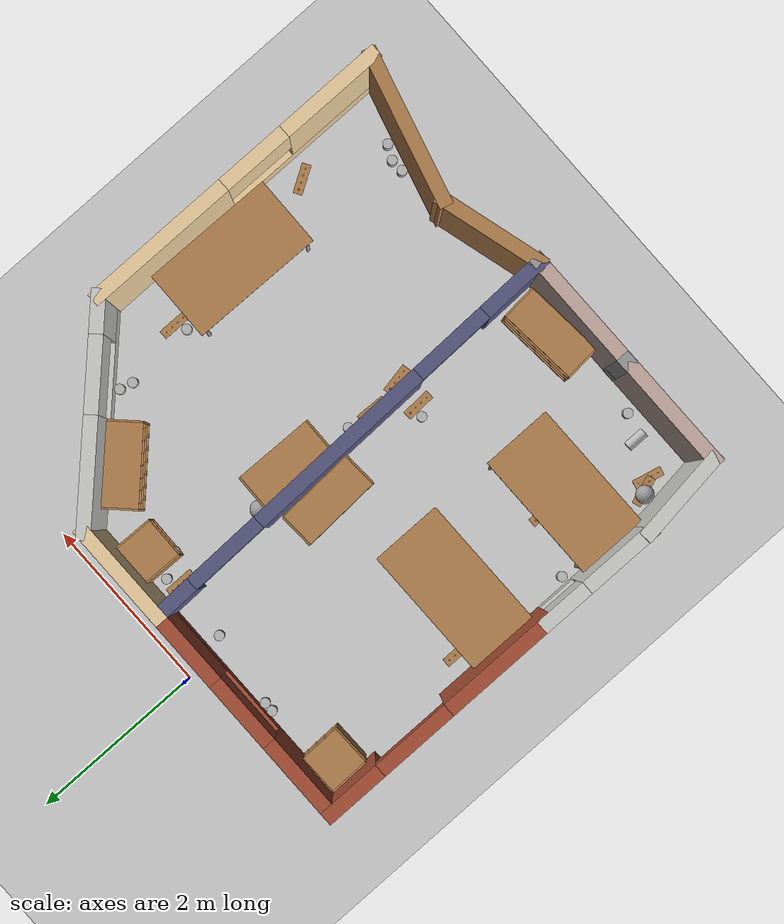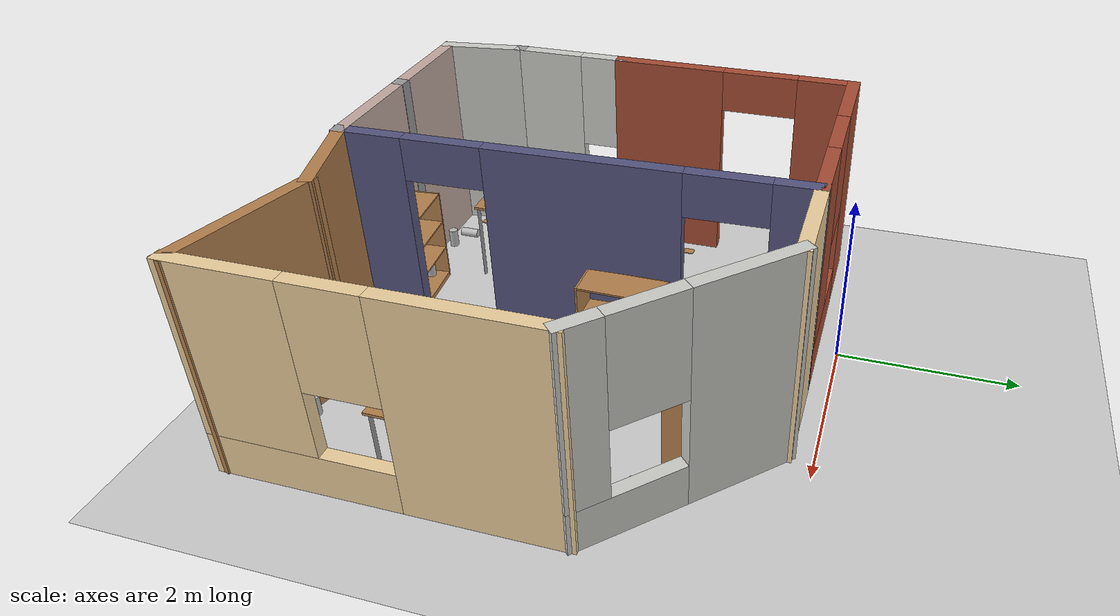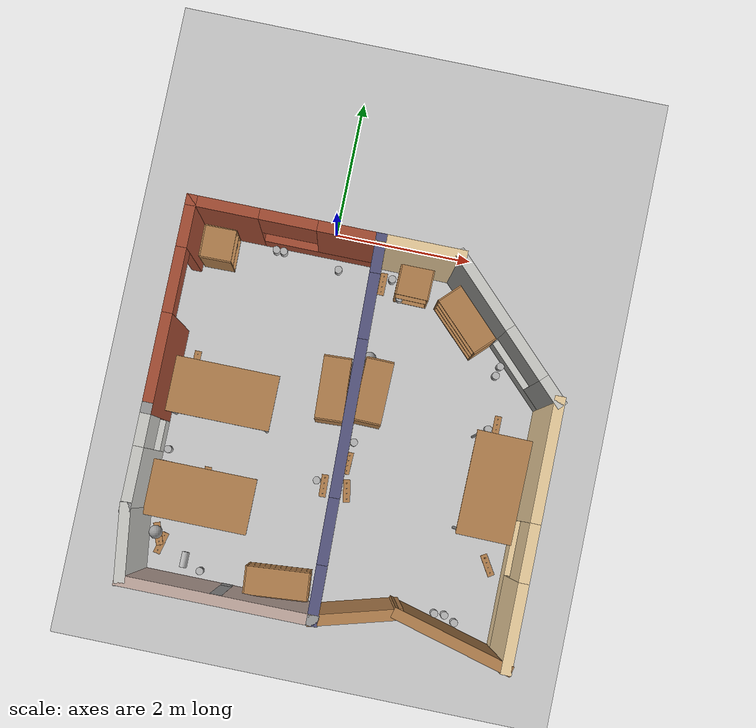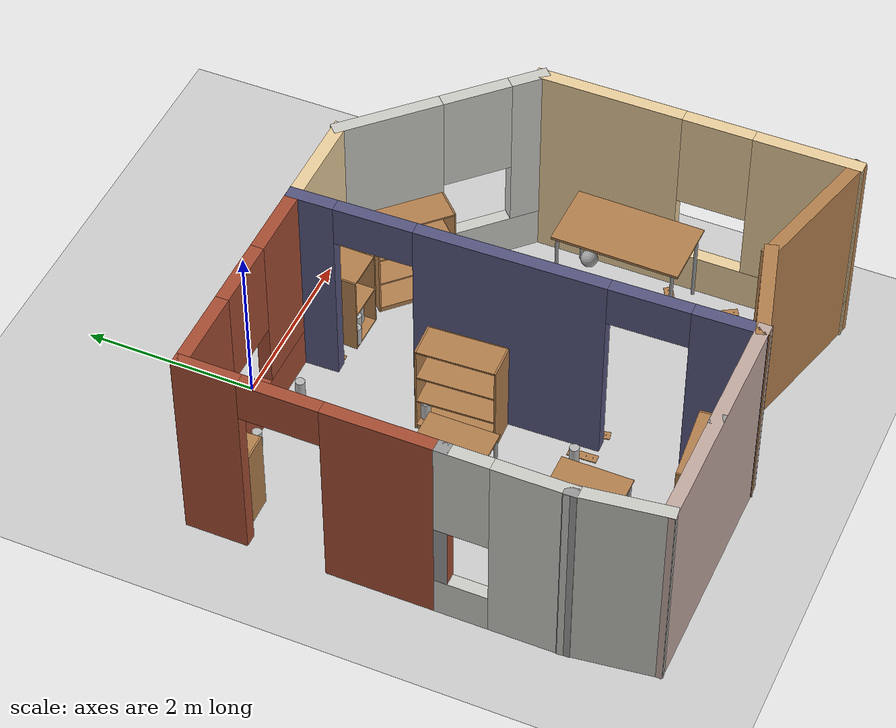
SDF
<sdf version="1.6">
 <world name="default">
  <light name="sun" type="directional">
   <pose>0 0 10 0 -0 0</pose>
   <diffuse>0.8 0.8 0.8 1</diffuse>
   <specular>0.2 0.2 0.2 1</specular>
   <attenuation>
    <range>1000</range>
    <constant>0.9</constant>
    <linear>0.01</linear>
    <quadratic>0.001</quadratic>
   </attenuation>
   <direction>-0.5 0.1 -0.9</direction>
  </light>
  <model name="ground_plane">
   <static>1</static>
   <link name="link">
    <collision name="collision">
     <geometry><plane><normal>0 0 1</normal><size>100 100</size></plane></geometry>
     <surface><friction><ode><mu>100</mu><mu2>50</mu2></ode></friction></surface>
    </collision>
    <visual name="visual">
     <cast_shadows>0</cast_shadows>
     <geometry><plane><normal>0 0 1</normal><size>100 100</size></plane></geometry>
     <material>
      <script><uri>file://media/materials/scripts/gazebo.material</uri><name>Gazebo/Grey</name></script>
     </material>
    </visual>
   </link>
  </model>
  <gravity>0 0 -9.8</gravity>
  <magnetic_field>6e-06 2.3e-05 -4.2e-05</magnetic_field>
  <atmosphere type="adiabatic"/>
  <physics name="default_physics" default="0" type="ode">
   <max_step_size>0.001</max_step_size>
   <real_time_factor>1</real_time_factor>
   <real_time_update_rate>1000</real_time_update_rate>
  </physics>
  <scene><ambient>0.4 0.4 0.4 1</ambient><background>0.7 0.7 0.7 1</background><shadows>1</shadows></scene>
  <spherical_coordinates>
   <surface_model>EARTH_WGS84</surface_model>
   <latitude_deg>0</latitude_deg>
   <longitude_deg>0</longitude_deg>
   <elevation>0</elevation>
   <heading_deg>0</heading_deg>
  </spherical_coordinates>
  <model name="OfficeMini">
   <pose>0.76074 -2.91797 0 0 -0 0</pose>
   <link name="Wall_0">
    <pose>-2.69182 -0.901255 0 0 -0 1.5708</pose>
    <visual name="Wall_0_Visual_0">
     <pose>-0.298988 0 1.25 0 -0 0</pose>
     <geometry><box><size>0.902024 0.15 2.5</size></box></geometry>
     <material>
      <script><uri>file://media/materials/scripts/gazebo.material</uri><name>Gazebo/CeilingTiled</name></script>
      <ambient>1 1 1 1</ambient>
     </material>
     <meta><layer>0</layer></meta>
    </visual>
    <collision name="Wall_0_Collision_0">
     <geometry><box><size>0.902024 0.15 2.5</size></box></geometry>
     <pose>-0.298988 0 1.25 0 -0 0</pose>
    </collision>
    <visual name="Wall_0_Visual_1">
     <pose>0.451012 0 0.25 0 -0 0</pose>
     <geometry><box><size>0.597976 0.15 0.5</size></box></geometry>
     <material>
      <script><uri>file://media/materials/scripts/gazebo.material</uri><name>Gazebo/CeilingTiled</name></script>
      <ambient>1 1 1 1</ambient>
     </material>
     <meta><layer>0</layer></meta>
    </visual>
    <collision name="Wall_0_Collision_1">
     <geometry><box><size>0.597976 0.15 0.5</size></box></geometry>
     <pose>0.451012 0 0.25 0 -0 0</pose>
    </collision>
    <visual name="Wall_0_Visual_2">
     <pose>0.451012 0 1.9 0 -0 0</pose>
     <geometry><box><size>0.597976 0.15 1.2</size></box></geometry>
     <material>
      <script><uri>file://media/materials/scripts/gazebo.material</uri><name>Gazebo/CeilingTiled</name></script>
      <ambient>1 1 1 1</ambient>
     </material>
     <meta><layer>0</layer></meta>
    </visual>
    <collision name="Wall_0_Collision_2">
     <geometry><box><size>0.597976 0.15 1.2</size></box></geometry>
     <pose>0.451012 0 1.9 0 -0 0</pose>
    </collision>
   </link>
   <link name="Wall_1">
    <collision name="Wall_1_Collision">
     <geometry><box><size>0.15 0.15 2.5</size></box></geometry>
     <pose>0 0 1.25 0 -0 0</pose>
    </collision>
    <visual name="Wall_1_Visual">
     <pose>0 0 1.25 0 -0 0</pose>
     <geometry><box><size>0.15 0.15 2.5</size></box></geometry>
     <material>
      <script><uri>file://media/materials/scripts/gazebo.material</uri><name>Gazebo/Grey</name></script>
      <ambient>1 1 1 1</ambient>
     </material>
     <meta><layer>0</layer></meta>
    </visual>
    <pose>-2.69182 -0.226255 0 0 -0 0</pose>
   </link>
   <link name="Wall_10">
    <collision name="Wall_10_Collision">
     <geometry><box><size>2.75 0.15 2.5</size></box></geometry>
     <pose>0 0 1.25 0 -0 0</pose>
    </collision>
    <visual name="Wall_10_Visual">
     <pose>0 0 1.25 0 -0 0</pose>
     <geometry><box><size>2.75 0.15 2.5</size></box></geometry>
     <material>
      <script><uri>file://media/materials/scripts/gazebo.material</uri><name>Gazebo/Grey</name></script>
      <ambient>0.760784 0.662745 0.627451 1</ambient>
     </material>
     <meta><layer>0</layer></meta>
    </visual>
    <pose>-1.26682 -2.52911 0 0 -0 3.14159</pose>
   </link>
   <link name="Wall_11">
    <collision name="Wall_11_Collision">
     <geometry><box><size>1.11102 0.15 2.5</size></box></geometry>
     <pose>0 0 1.25 0 -0 0</pose>
    </collision>
    <visual name="Wall_11_Visual">
     <pose>0 0 1.25 0 -0 0</pose>
     <geometry><box><size>1.11102 0.15 2.5</size></box></geometry>
     <material>
      <script><uri>file://media/materials/scripts/gazebo.material</uri><name>Gazebo/CeilingTiled</name></script>
      <ambient>1 1 1 1</ambient>
     </material>
     <meta><layer>0</layer></meta>
    </visual>
    <pose>-2.62932 -2.05268 0 0 -0 1.70124</pose>
   </link>
   <link name="Wall_12">
    <collision name="Wall_12_Collision">
     <geometry><box><size>0.15 0.15 2.5</size></box></geometry>
     <pose>0 0 1.25 0 -0 0</pose>
    </collision>
    <visual name="Wall_12_Visual">
     <pose>0 0 1.25 0 -0 0</pose>
     <geometry><box><size>0.15 0.15 2.5</size></box></geometry>
     <material>
      <script><uri>file://media/materials/scripts/gazebo.material</uri><name>Gazebo/Grey</name></script>
      <ambient>1 1 1 1</ambient>
     </material>
     <meta><layer>0</layer></meta>
    </visual>
    <pose>-2.69182 -1.57625 0 0 -0 0</pose>
   </link>
   <link name="Wall_16">
    <collision name="Wall_16_Collision">
     <geometry><box><size>0.16 0.15 2.5</size></box></geometry>
     <pose>0 0 1.25 0 -0 0</pose>
    </collision>
    <visual name="Wall_16_Visual">
     <pose>0 0 1.25 0 -0 0</pose>
     <geometry><box><size>0.16 0.15 2.5</size></box></geometry>
     <material>
      <script><uri>file://media/materials/scripts/gazebo.material</uri><name>Gazebo/Grey</name></script>
      <ambient>1 1 1 1</ambient>
     </material>
     <meta><layer>0</layer></meta>
    </visual>
    <pose>-1.28106 -2.52548 0 0 -0 0</pose>
   </link>
   <link name="Wall_17">
    <pose>-1.28106 -2.52548 0 0 -0 3.14159</pose>
    <visual name="Wall_17_Visual_0">
     <pose>0 0 0.25 0 -0 0</pose>
     <geometry><box><size>0.16 0.15 0.5</size></box></geometry>
     <material>
      <script><uri>file://media/materials/scripts/gazebo.material</uri><name>Gazebo/Grey</name></script>
      <ambient>1 1 1 1</ambient>
     </material>
     <meta><layer>0</layer></meta>
    </visual>
    <collision name="Wall_17_Collision_0">
     <geometry><box><size>0.16 0.15 0.5</size></box></geometry>
     <pose>0 0 0.25 0 -0 0</pose>
    </collision>
   </link>
   <link name="Wall_19">
    <collision name="Wall_19_Collision">
     <geometry><box><size>1.25 0.15 2.5</size></box></geometry>
     <pose>0 0 1.25 0 -0 0</pose>
    </collision>
    <visual name="Wall_19_Visual">
     <pose>0 0 1.25 0 -0 0</pose>
     <geometry><box><size>1.25 0.15 2.5</size></box></geometry>
     <material>
      <script><uri>file://media/materials/scripts/gazebo.material</uri><name>Gazebo/Grey</name></script>
      <ambient>0.921569 0.807843 0.615686 1</ambient>
     </material>
     <meta><layer>0</layer></meta>
    </visual>
    <pose>0.458176 2.62374 0 0 -0 0</pose>
   </link>
   <link name="Wall_20">
    <pose>1.83903 1.79289 0 0 0 -0.785398</pose>
    <visual name="Wall_20_Visual_0">
     <pose>-0.62706 0 1.25 0 -0 0</pose>
     <geometry><box><size>1.24588 0.15 2.5</size></box></geometry>
     <material>
      <script><uri>file://media/materials/scripts/gazebo.material</uri><name>Gazebo/CeilingTiled</name></script>
      <ambient>0.921569 0.807843 0.615686 1</ambient>
     </material>
     <meta><layer>0</layer></meta>
    </visual>
    <collision name="Wall_20_Collision_0">
     <geometry><box><size>1.24588 0.15 2.5</size></box></geometry>
     <pose>-0.62706 0 1.25 0 -0 0</pose>
    </collision>
    <visual name="Wall_20_Visual_1">
     <pose>0.62294 0 0.25 0 -0 0</pose>
     <geometry><box><size>1.25412 0.15 0.5</size></box></geometry>
     <material>
      <script><uri>file://media/materials/scripts/gazebo.material</uri><name>Gazebo/CeilingTiled</name></script>
      <ambient>0.921569 0.807843 0.615686 1</ambient>
     </material>
     <meta><layer>0</layer></meta>
    </visual>
    <collision name="Wall_20_Collision_1">
     <geometry><box><size>1.25412 0.15 0.5</size></box></geometry>
     <pose>0.62294 0 0.25 0 -0 0</pose>
    </collision>
    <visual name="Wall_20_Visual_2">
     <pose>1.02294 0 1.5 0 -0 0</pose>
     <geometry><box><size>0.454121 0.15 2</size></box></geometry>
     <material>
      <script><uri>file://media/materials/scripts/gazebo.material</uri><name>Gazebo/CeilingTiled</name></script>
      <ambient>0.921569 0.807843 0.615686 1</ambient>
     </material>
     <meta><layer>0</layer></meta>
    </visual>
    <collision name="Wall_20_Collision_2">
     <geometry><box><size>0.454121 0.15 2</size></box></geometry>
     <pose>1.02294 0 1.5 0 -0 0</pose>
    </collision>
    <visual name="Wall_20_Visual_3">
     <pose>0.395879 0 1.9 0 -0 0</pose>
     <geometry><box><size>0.8 0.15 1.2</size></box></geometry>
     <material>
      <script><uri>file://media/materials/scripts/gazebo.material</uri><name>Gazebo/CeilingTiled</name></script>
      <ambient>0.921569 0.807843 0.615686 1</ambient>
     </material>
     <meta><layer>0</layer></meta>
    </visual>
    <collision name="Wall_20_Collision_3">
     <geometry><box><size>0.8 0.15 1.2</size></box></geometry>
     <pose>0.395879 0 1.9 0 -0 0</pose>
    </collision>
   </link>
   <link name="Wall_21">
    <pose>2.66988 -0.837956 0 0 0 -1.5708</pose>
    <visual name="Wall_21_Visual_0">
     <pose>-1.01177 0 1.25 0 -0 0</pose>
     <geometry><box><size>1.72645 0.15 2.5</size></box></geometry>
     <material>
      <script><uri>file://media/materials/scripts/gazebo.material</uri><name>Gazebo/Grey</name></script>
      <ambient>0.921569 0.807843 0.615686 1</ambient>
     </material>
     <meta><layer>0</layer></meta>
    </visual>
    <collision name="Wall_21_Collision_0">
     <geometry><box><size>1.72645 0.15 2.5</size></box></geometry>
     <pose>-1.01177 0 1.25 0 -0 0</pose>
    </collision>
    <visual name="Wall_21_Visual_1">
     <pose>0.863227 0 0.25 0 -0 0</pose>
     <geometry><box><size>2.02355 0.15 0.5</size></box></geometry>
     <material>
      <script><uri>file://media/materials/scripts/gazebo.material</uri><name>Gazebo/Grey</name></script>
      <ambient>0.921569 0.807843 0.615686 1</ambient>
     </material>
     <meta><layer>0</layer></meta>
    </visual>
    <collision name="Wall_21_Collision_1">
     <geometry><box><size>2.02355 0.15 0.5</size></box></geometry>
     <pose>0.863227 0 0.25 0 -0 0</pose>
    </collision>
    <visual name="Wall_21_Visual_2">
     <pose>1.26323 0 1.5 0 -0 0</pose>
     <geometry><box><size>1.22355 0.15 2</size></box></geometry>
     <material>
      <script><uri>file://media/materials/scripts/gazebo.material</uri><name>Gazebo/Grey</name></script>
      <ambient>0.921569 0.807843 0.615686 1</ambient>
     </material>
     <meta><layer>0</layer></meta>
    </visual>
    <collision name="Wall_21_Collision_2">
     <geometry><box><size>1.22355 0.15 2</size></box></geometry>
     <pose>1.26323 0 1.5 0 -0 0</pose>
    </collision>
    <visual name="Wall_21_Visual_3">
     <pose>0.251454 0 1.9 0 -0 0</pose>
     <geometry><box><size>0.8 0.15 1.2</size></box></geometry>
     <material>
      <script><uri>file://media/materials/scripts/gazebo.material</uri><name>Gazebo/Grey</name></script>
      <ambient>0.921569 0.807843 0.615686 1</ambient>
     </material>
     <meta><layer>0</layer></meta>
    </visual>
    <collision name="Wall_21_Collision_3">
     <geometry><box><size>0.8 0.15 1.2</size></box></geometry>
     <pose>0.251454 0 1.9 0 -0 0</pose>
    </collision>
   </link>
   <link name="Wall_22">
    <collision name="Wall_22_Collision">
     <geometry><box><size>1.75 0.15 2.5</size></box></geometry>
     <pose>0 0 1.25 0 -0 0</pose>
    </collision>
    <visual name="Wall_22_Visual">
     <pose>0 0 1.25 0 -0 0</pose>
     <geometry><box><size>1.75 0.15 2.5</size></box></geometry>
     <material>
      <script><uri>file://media/materials/scripts/gazebo.material</uri><name>Gazebo/Wood</name></script>
      <ambient>1 1 1 1</ambient>
     </material>
     <meta><layer>0</layer></meta>
    </visual>
    <pose>1.89714 -2.4309 0 0 -0 2.87979</pose>
   </link>
   <link name="Wall_23">
    <collision name="Wall_23_Collision">
     <geometry><box><size>1.28311 0.15 2.5</size></box></geometry>
     <pose>0 0 1.25 0 -0 0</pose>
    </collision>
    <visual name="Wall_23_Visual">
     <pose>0 0 1.25 0 -0 0</pose>
     <geometry><box><size>1.28311 0.15 2.5</size></box></geometry>
     <material>
      <script><uri>file://media/materials/scripts/gazebo.material</uri><name>Gazebo/Wood</name></script>
      <ambient>1 1 1 1</ambient>
     </material>
     <meta><layer>0</layer></meta>
    </visual>
    <pose>0.578785 -2.37648 0 0 0 -2.86882</pose>
   </link>
   <link name="Wall_24">
    <collision name="Wall_24_Collision">
     <geometry><box><size>0.15 0.15 2.5</size></box></geometry>
     <pose>0 0 1.25 0 -0 0</pose>
    </collision>
    <visual name="Wall_24_Visual">
     <pose>0 0 1.25 0 -0 0</pose>
     <geometry><box><size>0.15 0.15 2.5</size></box></geometry>
     <material>
      <script><uri>file://media/materials/scripts/gazebo.material</uri><name>Gazebo/Grey</name></script>
      <ambient>1 1 1 1</ambient>
     </material>
     <meta><layer>0</layer></meta>
    </visual>
    <pose>0.033176 -2.52911 0 0 -0 0</pose>
   </link>
   <link name="Wall_26">
    <pose>-0.029324 0.04732 0 0 0 -1.54654</pose>
    <visual name="Wall_26_Visual_0">
     <pose>-2.37982 0 1.25 0 -0 0</pose>
     <geometry><box><size>0.544731 0.15 2.5</size></box></geometry>
     <material>
      <script><uri>file://media/materials/scripts/gazebo.material</uri><name>Gazebo/Grey</name></script>
      <ambient>0.333333 0.333333 0.498039 1</ambient>
     </material>
     <meta><layer>0</layer></meta>
    </visual>
    <collision name="Wall_26_Collision_0">
     <geometry><box><size>0.544731 0.15 2.5</size></box></geometry>
     <pose>-2.37982 0 1.25 0 -0 0</pose>
    </collision>
    <visual name="Wall_26_Visual_1">
     <pose>-0.133525 0 1.25 0 -0 0</pose>
     <geometry><box><size>2.14785 0.15 2.5</size></box></geometry>
     <material>
      <script><uri>file://media/materials/scripts/gazebo.material</uri><name>Gazebo/Grey</name></script>
      <ambient>0.333333 0.333333 0.498039 1</ambient>
     </material>
     <meta><layer>0</layer></meta>
    </visual>
    <collision name="Wall_26_Collision_1">
     <geometry><box><size>2.14785 0.15 2.5</size></box></geometry>
     <pose>-0.133525 0 1.25 0 -0 0</pose>
    </collision>
    <visual name="Wall_26_Visual_2">
     <pose>2.24629 0 1.25 0 -0 0</pose>
     <geometry><box><size>0.811781 0.15 2.5</size></box></geometry>
     <material>
      <script><uri>file://media/materials/scripts/gazebo.material</uri><name>Gazebo/Grey</name></script>
      <ambient>0.333333 0.333333 0.498039 1</ambient>
     </material>
     <meta><layer>0</layer></meta>
    </visual>
    <collision name="Wall_26_Collision_2">
     <geometry><box><size>0.811781 0.15 2.5</size></box></geometry>
     <pose>2.24629 0 1.25 0 -0 0</pose>
    </collision>
    <visual name="Wall_26_Visual_3">
     <pose>-1.65745 0 2.25 0 -0 0</pose>
     <geometry><box><size>0.9 0.15 0.5</size></box></geometry>
     <material>
      <script><uri>file://media/materials/scripts/gazebo.material</uri><name>Gazebo/Grey</name></script>
      <ambient>0.333333 0.333333 0.498039 1</ambient>
     </material>
     <meta><layer>0</layer></meta>
    </visual>
    <collision name="Wall_26_Collision_3">
     <geometry><box><size>0.9 0.15 0.5</size></box></geometry>
     <pose>-1.65745 0 2.25 0 -0 0</pose>
    </collision>
    <visual name="Wall_26_Visual_4">
     <pose>1.3904 0 2.25 0 -0 0</pose>
     <geometry><box><size>0.9 0.15 0.5</size></box></geometry>
     <material>
      <script><uri>file://media/materials/scripts/gazebo.material</uri><name>Gazebo/Grey</name></script>
      <ambient>0.333333 0.333333 0.498039 1</ambient>
     </material>
     <meta><layer>0</layer></meta>
    </visual>
    <collision name="Wall_26_Collision_4">
     <geometry><box><size>0.9 0.15 0.5</size></box></geometry>
     <pose>1.3904 0 2.25 0 -0 0</pose>
    </collision>
   </link>
   <link name="Wall_27">
    <collision name="Wall_27_Collision">
     <geometry><box><size>0.16 0.15 2.5</size></box></geometry>
     <pose>0 0 1.25 0 -0 0</pose>
    </collision>
    <visual name="Wall_27_Visual">
     <pose>0 0 1.25 0 -0 0</pose>
     <geometry><box><size>0.16 0.15 2.5</size></box></geometry>
     <material>
      <script><uri>file://media/materials/scripts/gazebo.material</uri><name>Gazebo/Grey</name></script>
      <ambient>1 1 1 1</ambient>
     </material>
     <meta><layer>0</layer></meta>
    </visual>
    <pose>0.038176 -2.52911 0 0 -0 0</pose>
   </link>
   <link name="Wall_4">
    <pose>-2.69182 1.19874 0 0 -0 1.5708</pose>
    <visual name="Wall_4_Visual_0">
     <pose>-0.812198 0 1.25 0 -0 0</pose>
     <geometry><box><size>1.3756 0.15 2.5</size></box></geometry>
     <material>
      <script><uri>file://media/materials/scripts/gazebo.material</uri><name>Gazebo/Bricks</name></script>
      <ambient>1 1 1 1</ambient>
     </material>
     <meta><layer>0</layer></meta>
    </visual>
    <collision name="Wall_4_Collision_0">
     <geometry><box><size>1.3756 0.15 2.5</size></box></geometry>
     <pose>-0.812198 0 1.25 0 -0 0</pose>
    </collision>
    <visual name="Wall_4_Visual_1">
     <pose>1.1378 0 1.25 0 -0 0</pose>
     <geometry><box><size>0.724396 0.15 2.5</size></box></geometry>
     <material>
      <script><uri>file://media/materials/scripts/gazebo.material</uri><name>Gazebo/Bricks</name></script>
      <ambient>1 1 1 1</ambient>
     </material>
     <meta><layer>0</layer></meta>
    </visual>
    <collision name="Wall_4_Collision_1">
     <geometry><box><size>0.724396 0.15 2.5</size></box></geometry>
     <pose>1.1378 0 1.25 0 -0 0</pose>
    </collision>
    <visual name="Wall_4_Visual_2">
     <pose>0.325604 0 2.25 0 -0 0</pose>
     <geometry><box><size>0.9 0.15 0.5</size></box></geometry>
     <material>
      <script><uri>file://media/materials/scripts/gazebo.material</uri><name>Gazebo/Bricks</name></script>
      <ambient>1 1 1 1</ambient>
     </material>
     <meta><layer>0</layer></meta>
    </visual>
    <collision name="Wall_4_Collision_2">
     <geometry><box><size>0.9 0.15 0.5</size></box></geometry>
     <pose>0.325604 0 2.25 0 -0 0</pose>
    </collision>
   </link>
   <link name="Wall_5">
    <pose>-1.39182 2.62374 0 0 -0 0</pose>
    <visual name="Wall_5_Visual_0">
     <pose>-0.87278 0 1.25 0 -0 0</pose>
     <geometry><box><size>1.00444 0.15 2.5</size></box></geometry>
     <material>
      <script><uri>file://media/materials/scripts/gazebo.material</uri><name>Gazebo/Bricks</name></script>
      <ambient>1 1 1 1</ambient>
     </material>
     <meta><layer>0</layer></meta>
    </visual>
    <collision name="Wall_5_Collision_0">
     <geometry><box><size>1.00444 0.15 2.5</size></box></geometry>
     <pose>-0.87278 0 1.25 0 -0 0</pose>
    </collision>
    <visual name="Wall_5_Visual_1">
     <pose>0.50222 0 0.25 0 -0 0</pose>
     <geometry><box><size>1.74556 0.15 0.5</size></box></geometry>
     <material>
      <script><uri>file://media/materials/scripts/gazebo.material</uri><name>Gazebo/Bricks</name></script>
      <ambient>1 1 1 1</ambient>
     </material>
     <meta><layer>0</layer></meta>
    </visual>
    <collision name="Wall_5_Collision_1">
     <geometry><box><size>1.74556 0.15 0.5</size></box></geometry>
     <pose>0.50222 0 0.25 0 -0 0</pose>
    </collision>
    <visual name="Wall_5_Visual_2">
     <pose>0.90222 0 1.5 0 -0 0</pose>
     <geometry><box><size>0.94556 0.15 2</size></box></geometry>
     <material>
      <script><uri>file://media/materials/scripts/gazebo.material</uri><name>Gazebo/Bricks</name></script>
      <ambient>1 1 1 1</ambient>
     </material>
     <meta><layer>0</layer></meta>
    </visual>
    <collision name="Wall_5_Collision_2">
     <geometry><box><size>0.94556 0.15 2</size></box></geometry>
     <pose>0.90222 0 1.5 0 -0 0</pose>
    </collision>
    <visual name="Wall_5_Visual_3">
     <pose>0.02944 0 1.9 0 -0 0</pose>
     <geometry><box><size>0.8 0.15 1.2</size></box></geometry>
     <material>
      <script><uri>file://media/materials/scripts/gazebo.material</uri><name>Gazebo/Bricks</name></script>
      <ambient>1 1 1 1</ambient>
     </material>
     <meta><layer>0</layer></meta>
    </visual>
    <collision name="Wall_5_Collision_3">
     <geometry><box><size>0.8 0.15 1.2</size></box></geometry>
     <pose>0.02944 0 1.9 0 -0 0</pose>
    </collision>
   </link>
   <link name="Wall_9">
    <collision name="Wall_9_Collision">
     <geometry><box><size>0.15 0.15 2.5</size></box></geometry>
     <pose>0 0 1.25 0 -0 0</pose>
    </collision>
    <visual name="Wall_9_Visual">
     <pose>0 0 1.25 0 -0 0</pose>
     <geometry><box><size>0.15 0.15 2.5</size></box></geometry>
     <material>
      <script><uri>file://media/materials/scripts/gazebo.material</uri><name>Gazebo/Grey</name></script>
      <ambient>1 1 1 1</ambient>
     </material>
     <meta><layer>0</layer></meta>
    </visual>
    <pose>0.033176 -2.52911 0 0 -0 0</pose>
   </link>
   <static>1</static>
  </model>
  <model name="table">
   <static>1</static>
   <link name="link">
    <collision name="surface">
     <pose>0 0 1 0 -0 0</pose>
     <geometry><box><size>1.5 0.8 0.03</size></box></geometry>
     <surface><friction><ode><mu>0.6</mu><mu2>0.6</mu2></ode></friction></surface>
    </collision>
    <visual name="visual1">
     <pose>0 0 1 0 -0 0</pose>
     <geometry><box><size>1.5 0.8 0.03</size></box></geometry>
     <material>
      <script><uri>file://media/materials/scripts/gazebo.material</uri><name>Gazebo/Wood</name></script>
     </material>
    </visual>
    <collision name="front_left_leg">
     <pose>0.68 0.38 0.5 0 -0 0</pose>
     <geometry><cylinder><radius>0.02</radius><length>1</length></cylinder></geometry>
    </collision>
    <visual name="front_left_leg">
     <pose>0.68 0.38 0.5 0 -0 0</pose>
     <geometry><cylinder><radius>0.02</radius><length>1</length></cylinder></geometry>
     <material>
      <script><uri>file://media/materials/scripts/gazebo.material</uri><name>Gazebo/Grey</name></script>
     </material>
    </visual>
    <collision name="front_right_leg">
     <pose>0.68 -0.38 0.5 0 -0 0</pose>
     <geometry><cylinder><radius>0.02</radius><length>1</length></cylinder></geometry>
    </collision>
    <visual name="front_right_leg">
     <pose>0.68 -0.38 0.5 0 -0 0</pose>
     <geometry><cylinder><radius>0.02</radius><length>1</length></cylinder></geometry>
     <material>
      <script><uri>file://media/materials/scripts/gazebo.material</uri><name>Gazebo/Grey</name></script>
     </material>
    </visual>
    <collision name="back_right_leg">
     <pose>-0.68 -0.38 0.5 0 -0 0</pose>
     <geometry><cylinder><radius>0.02</radius><length>1</length></cylinder></geometry>
    </collision>
    <visual name="back_right_leg">
     <pose>-0.68 -0.38 0.5 0 -0 0</pose>
     <geometry><cylinder><radius>0.02</radius><length>1</length></cylinder></geometry>
     <material>
      <script><uri>file://media/materials/scripts/gazebo.material</uri><name>Gazebo/Grey</name></script>
     </material>
    </visual>
    <collision name="back_left_leg">
     <pose>-0.68 0.38 0.5 0 -0 0</pose>
     <geometry><cylinder><radius>0.02</radius><length>1</length></cylinder></geometry>
    </collision>
    <visual name="back_left_leg">
     <pose>-0.68 0.38 0.5 0 -0 0</pose>
     <geometry><cylinder><radius>0.02</radius><length>1</length></cylinder></geometry>
     <material>
      <script><uri>file://media/materials/scripts/gazebo.material</uri><name>Gazebo/Grey</name></script>
     </material>
    </visual>
   </link>
   <pose>-1.11658 -4.18409 0 0 -0 0</pose>
  </model>
  <model name="table_0">
   <static>1</static>
   <link name="link">
    <collision name="surface">
     <pose>0 0 1 0 -0 0</pose>
     <geometry><box><size>1.5 0.8 0.03</size></box></geometry>
     <surface><friction><ode><mu>0.6</mu><mu2>0.6</mu2></ode></friction></surface>
    </collision>
    <visual name="visual1">
     <pose>0 0 1 0 -0 0</pose>
     <geometry><box><size>1.5 0.8 0.03</size></box></geometry>
     <material>
      <script><uri>file://media/materials/scripts/gazebo.material</uri><name>Gazebo/Wood</name></script>
     </material>
    </visual>
    <collision name="front_left_leg">
     <pose>0.68 0.38 0.5 0 -0 0</pose>
     <geometry><cylinder><radius>0.02</radius><length>1</length></cylinder></geometry>
    </collision>
    <visual name="front_left_leg">
     <pose>0.68 0.38 0.5 0 -0 0</pose>
     <geometry><cylinder><radius>0.02</radius><length>1</length></cylinder></geometry>
     <material>
      <script><uri>file://media/materials/scripts/gazebo.material</uri><name>Gazebo/Grey</name></script>
     </material>
    </visual>
    <collision name="front_right_leg">
     <pose>0.68 -0.38 0.5 0 -0 0</pose>
     <geometry><cylinder><radius>0.02</radius><length>1</length></cylinder></geometry>
    </collision>
    <visual name="front_right_leg">
     <pose>0.68 -0.38 0.5 0 -0 0</pose>
     <geometry><cylinder><radius>0.02</radius><length>1</length></cylinder></geometry>
     <material>
      <script><uri>file://media/materials/scripts/gazebo.material</uri><name>Gazebo/Grey</name></script>
     </material>
    </visual>
    <collision name="back_right_leg">
     <pose>-0.68 -0.38 0.5 0 -0 0</pose>
     <geometry><cylinder><radius>0.02</radius><length>1</length></cylinder></geometry>
    </collision>
    <visual name="back_right_leg">
     <pose>-0.68 -0.38 0.5 0 -0 0</pose>
     <geometry><cylinder><radius>0.02</radius><length>1</length></cylinder></geometry>
     <material>
      <script><uri>file://media/materials/scripts/gazebo.material</uri><name>Gazebo/Grey</name></script>
     </material>
    </visual>
    <collision name="back_left_leg">
     <pose>-0.68 0.38 0.5 0 -0 0</pose>
     <geometry><cylinder><radius>0.02</radius><length>1</length></cylinder></geometry>
    </collision>
    <visual name="back_left_leg">
     <pose>-0.68 0.38 0.5 0 -0 0</pose>
     <geometry><cylinder><radius>0.02</radius><length>1</length></cylinder></geometry>
     <material>
      <script><uri>file://media/materials/scripts/gazebo.material</uri><name>Gazebo/Grey</name></script>
     </material>
    </visual>
   </link>
   <pose>-1.10075 -2.69015 0 0 -0 0</pose>
  </model>
  <model name="cabinet">
   <static>1</static>
   <link name="cabinet_bottom_plate">
    <inertial>
     <pose>0 0 -1 0 -0 0</pose>
     <inertia><ixx>2.05</ixx><ixy>0</ixy><ixz>0</ixz><iyy>2.05</iyy><iyz>0</iyz><izz>2.05</izz></inertia>
     <mass>25</mass>
    </inertial>
    <collision name="cabinet_bottom_plate_geom">
     <pose>0 0 0.01 0 -0 0</pose>
     <geometry><box><size>0.45 0.45 0.02</size></box></geometry>
    </collision>
    <visual name="cabinet_bottom_plate_geom_visual">
     <pose>0 0 0.01 0 -0 0</pose>
     <geometry><box><size>0.45 0.45 0.02</size></box></geometry>
     <material>
      <script><uri>file://media/materials/scripts/gazebo.material</uri><name>Gazebo/Wood</name></script>
     </material>
    </visual>
    <collision name="cabinet_bottom_plate_geom_cabinet_back_plate">
     <pose>0.235 0 0.51 0 -0 0</pose>
     <geometry><box><size>0.02 0.45 1.02</size></box></geometry>
    </collision>
    <visual name="cabinet_bottom_plate_geom_cabinet_back_plate_visual">
     <pose>0.235 0 0.51 0 -0 0</pose>
     <geometry><box><size>0.02 0.45 1.02</size></box></geometry>
     <material>
      <script><uri>file://media/materials/scripts/gazebo.material</uri><name>Gazebo/Wood</name></script>
     </material>
    </visual>
    <collision name="cabinet_bottom_plate_geom_cabinet_left_plate">
     <pose>0 0.235 0.51 0 -0 0</pose>
     <geometry><box><size>0.45 0.02 1.02</size></box></geometry>
    </collision>
    <visual name="cabinet_bottom_plate_geom_cabinet_left_plate_visual">
     <pose>0 0.235 0.51 0 -0 0</pose>
     <geometry><box><size>0.45 0.02 1.02</size></box></geometry>
     <material>
      <script><uri>file://media/materials/scripts/gazebo.material</uri><name>Gazebo/Wood</name></script>
     </material>
    </visual>
    <collision name="cabinet_bottom_plate_geom_cabinet_middle_plate">
     <pose>0 0 0.51 0 -0 0</pose>
     <geometry><box><size>0.45 0.45 0.02</size></box></geometry>
    </collision>
    <visual name="cabinet_bottom_plate_geom_cabinet_middle_plate_visual">
     <pose>0 0 0.51 0 -0 0</pose>
     <geometry><box><size>0.45 0.45 0.02</size></box></geometry>
     <material>
      <script><uri>file://media/materials/scripts/gazebo.material</uri><name>Gazebo/Wood</name></script>
     </material>
    </visual>
    <collision name="cabinet_bottom_plate_geom_cabinet_right_plate">
     <pose>0 -0.235 0.51 0 -0 0</pose>
     <geometry><box><size>0.45 0.02 1.02</size></box></geometry>
    </collision>
    <visual name="cabinet_bottom_plate_geom_cabinet_right_plate_visual">
     <pose>0 -0.235 0.51 0 -0 0</pose>
     <geometry><box><size>0.45 0.02 1.02</size></box></geometry>
     <material>
      <script><uri>file://media/materials/scripts/gazebo.material</uri><name>Gazebo/Wood</name></script>
     </material>
    </visual>
    <collision name="cabinet_bottom_plate_geom_cabinet_top_plate">
     <pose>0 0 1.01 0 -0 0</pose>
     <geometry><box><size>0.45 0.45 0.02</size></box></geometry>
    </collision>
    <visual name="cabinet_bottom_plate_geom_cabinet_top_plate_visual">
     <pose>0 0 1.01 0 -0 0</pose>
     <geometry><box><size>0.45 0.45 0.02</size></box></geometry>
     <material>
      <script><uri>file://media/materials/scripts/gazebo.material</uri><name>Gazebo/Wood</name></script>
     </material>
    </visual>
   </link>
   <pose>-1.60346 -0.606793 0 0 0 -3.12567</pose>
  </model>
  <model name="bookshelf">
   <static>1</static>
   <link name="link">
    <inertial><mass>1</mass></inertial>
    <collision name="back">
     <pose>0 0.005 0.6 0 -0 0</pose>
     <geometry><box><size>0.9 0.01 1.2</size></box></geometry>
    </collision>
    <visual name="visual1">
     <pose>0 0.005 0.6 0 -0 0</pose>
     <geometry><box><size>0.9 0.01 1.2</size></box></geometry>
     <material>
      <script><uri>file://media/materials/scripts/gazebo.material</uri><name>Gazebo/Wood</name></script>
     </material>
    </visual>
    <collision name="left_side">
     <pose>0.45 -0.195 0.6 0 -0 0</pose>
     <geometry><box><size>0.02 0.4 1.2</size></box></geometry>
    </collision>
    <visual name="visual2">
     <pose>0.45 -0.195 0.6 0 -0 0</pose>
     <geometry><box><size>0.02 0.4 1.2</size></box></geometry>
     <material>
      <script><uri>file://media/materials/scripts/gazebo.material</uri><name>Gazebo/Wood</name></script>
     </material>
    </visual>
    <collision name="right_side">
     <pose>-0.45 -0.195 0.6 0 -0 0</pose>
     <geometry><box><size>0.02 0.4 1.2</size></box></geometry>
    </collision>
    <visual name="visual3">
     <pose>-0.45 -0.195 0.6 0 -0 0</pose>
     <geometry><box><size>0.02 0.4 1.2</size></box></geometry>
     <material>
      <script><uri>file://media/materials/scripts/gazebo.material</uri><name>Gazebo/Wood</name></script>
     </material>
    </visual>
    <collision name="bottom">
     <pose>0 -0.195 0.03 0 -0 0</pose>
     <geometry><box><size>0.88 0.4 0.06</size></box></geometry>
    </collision>
    <visual name="visual4">
     <pose>0 -0.195 0.03 0 -0 0</pose>
     <geometry><box><size>0.88 0.4 0.06</size></box></geometry>
     <material>
      <script><uri>file://media/materials/scripts/gazebo.material</uri><name>Gazebo/Wood</name></script>
     </material>
    </visual>
    <collision name="top">
     <pose>0 -0.195 1.19 0 -0 0</pose>
     <geometry><box><size>0.88 0.4 0.02</size></box></geometry>
    </collision>
    <visual name="visual5">
     <pose>0 -0.195 1.19 0 -0 0</pose>
     <geometry><box><size>0.88 0.4 0.02</size></box></geometry>
     <material>
      <script><uri>file://media/materials/scripts/gazebo.material</uri><name>Gazebo/Wood</name></script>
     </material>
    </visual>
    <collision name="low_shelf">
     <pose>0 -0.195 0.43 0 -0 0</pose>
     <geometry><box><size>0.88 0.4 0.02</size></box></geometry>
    </collision>
    <visual name="visual6">
     <pose>0 -0.195 0.43 0 -0 0</pose>
     <geometry><box><size>0.88 0.4 0.02</size></box></geometry>
     <material>
      <script><uri>file://media/materials/scripts/gazebo.material</uri><name>Gazebo/Wood</name></script>
     </material>
    </visual>
    <collision name="high_shelf">
     <pose>0 -0.195 0.8 0 -0 0</pose>
     <geometry><box><size>0.88 0.4 0.02</size></box></geometry>
    </collision>
    <visual name="visual7">
     <pose>0 -0.195 0.8 0 -0 0</pose>
     <geometry><box><size>0.88 0.4 0.02</size></box></geometry>
     <material>
      <script><uri>file://media/materials/scripts/gazebo.material</uri><name>Gazebo/Wood</name></script>
     </material>
    </visual>
   </link>
   <pose>0.218559 -5.34218 0 0 0 -3.056</pose>
  </model>
  <model name="bookshelf_0">
   <static>1</static>
   <link name="link">
    <inertial><mass>1</mass></inertial>
    <collision name="back">
     <pose>0 0.005 0.6 0 -0 0</pose>
     <geometry><box><size>0.9 0.01 1.2</size></box></geometry>
    </collision>
    <visual name="visual1">
     <pose>0 0.005 0.6 0 -0 0</pose>
     <geometry><box><size>0.9 0.01 1.2</size></box></geometry>
     <material>
      <script><uri>file://media/materials/scripts/gazebo.material</uri><name>Gazebo/Wood</name></script>
     </material>
    </visual>
    <collision name="left_side">
     <pose>0.45 -0.195 0.6 0 -0 0</pose>
     <geometry><box><size>0.02 0.4 1.2</size></box></geometry>
    </collision>
    <visual name="visual2">
     <pose>0.45 -0.195 0.6 0 -0 0</pose>
     <geometry><box><size>0.02 0.4 1.2</size></box></geometry>
     <material>
      <script><uri>file://media/materials/scripts/gazebo.material</uri><name>Gazebo/Wood</name></script>
     </material>
    </visual>
    <collision name="right_side">
     <pose>-0.45 -0.195 0.6 0 -0 0</pose>
     <geometry><box><size>0.02 0.4 1.2</size></box></geometry>
    </collision>
    <visual name="visual3">
     <pose>-0.45 -0.195 0.6 0 -0 0</pose>
     <geometry><box><size>0.02 0.4 1.2</size></box></geometry>
     <material>
      <script><uri>file://media/materials/scripts/gazebo.material</uri><name>Gazebo/Wood</name></script>
     </material>
    </visual>
    <collision name="bottom">
     <pose>0 -0.195 0.03 0 -0 0</pose>
     <geometry><box><size>0.88 0.4 0.06</size></box></geometry>
    </collision>
    <visual name="visual4">
     <pose>0 -0.195 0.03 0 -0 0</pose>
     <geometry><box><size>0.88 0.4 0.06</size></box></geometry>
     <material>
      <script><uri>file://media/materials/scripts/gazebo.material</uri><name>Gazebo/Wood</name></script>
     </material>
    </visual>
    <collision name="top">
     <pose>0 -0.195 1.19 0 -0 0</pose>
     <geometry><box><size>0.88 0.4 0.02</size></box></geometry>
    </collision>
    <visual name="visual5">
     <pose>0 -0.195 1.19 0 -0 0</pose>
     <geometry><box><size>0.88 0.4 0.02</size></box></geometry>
     <material>
      <script><uri>file://media/materials/scripts/gazebo.material</uri><name>Gazebo/Wood</name></script>
     </material>
    </visual>
    <collision name="low_shelf">
     <pose>0 -0.195 0.43 0 -0 0</pose>
     <geometry><box><size>0.88 0.4 0.02</size></box></geometry>
    </collision>
    <visual name="visual6">
     <pose>0 -0.195 0.43 0 -0 0</pose>
     <geometry><box><size>0.88 0.4 0.02</size></box></geometry>
     <material>
      <script><uri>file://media/materials/scripts/gazebo.material</uri><name>Gazebo/Wood</name></script>
     </material>
    </visual>
    <collision name="high_shelf">
     <pose>0 -0.195 0.8 0 -0 0</pose>
     <geometry><box><size>0.88 0.4 0.02</size></box></geometry>
    </collision>
    <visual name="visual7">
     <pose>0 -0.195 0.8 0 -0 0</pose>
     <geometry><box><size>0.88 0.4 0.02</size></box></geometry>
     <material>
      <script><uri>file://media/materials/scripts/gazebo.material</uri><name>Gazebo/Wood</name></script>
     </material>
    </visual>
   </link>
   <pose>0.619209 -2.30664 0 0 0 -1.52324</pose>
  </model>
  <model name="beer">
   <link name="link">
    <pose>0 0 0.115 0 -0 0</pose>
    <inertial>
     <mass>0.39</mass>
     <inertia><ixx>0.00058</ixx><ixy>0</ixy><ixz>0</ixz><iyy>0.00058</iyy><iyz>0</iyz><izz>0.00019</izz></inertia>
    </inertial>
    <collision name="collision">
     <geometry><cylinder><radius>0.055</radius><length>0.23</length></cylinder></geometry>
    </collision>
    <visual name="visual">
     <geometry><cylinder><radius>0.055</radius><length>0.23</length></cylinder></geometry>
     <material>
      <script>
       <uri>model://beer/materials/scripts</uri>
       <uri>model://beer/materials/textures</uri>
       <name>Beer/Diffuse</name>
      </script>
     </material>
    </visual>
   </link>
   <pose>0.127018 -0.530351 -7e-06 -1e-06 -0 -0.00014</pose>
  </model>
  <model name="beer_0">
   <link name="link">
    <pose>0 0 0.115 0 -0 0</pose>
    <inertial>
     <mass>0.39</mass>
     <inertia><ixx>0.00058</ixx><ixy>0</ixy><ixz>0</ixz><iyy>0.00058</iyy><iyz>0</iyz><izz>0.00019</izz></inertia>
    </inertial>
    <collision name="collision">
     <geometry><cylinder><radius>0.055</radius><length>0.23</length></cylinder></geometry>
    </collision>
    <visual name="visual">
     <geometry><cylinder><radius>0.055</radius><length>0.23</length></cylinder></geometry>
     <material>
      <script>
       <uri>model://beer/materials/scripts</uri>
       <uri>model://beer/materials/textures</uri>
       <name>Beer/Diffuse</name>
      </script>
     </material>
    </visual>
   </link>
   <pose>-0.825052 -0.42424 -2e-06 1e-06 -0 0.056134</pose>
  </model>
  <model name="beer_1">
   <link name="link">
    <pose>0 0 0.115 0 -0 0</pose>
    <inertial>
     <mass>0.39</mass>
     <inertia><ixx>0.00058</ixx><ixy>0</ixy><ixz>0</ixz><iyy>0.00058</iyy><iyz>0</iyz><izz>0.00019</izz></inertia>
    </inertial>
    <collision name="collision">
     <geometry><cylinder><radius>0.055</radius><length>0.23</length></cylinder></geometry>
    </collision>
    <visual name="visual">
     <geometry><cylinder><radius>0.055</radius><length>0.23</length></cylinder></geometry>
     <material>
      <script>
       <uri>model://beer/materials/scripts</uri>
       <uri>model://beer/materials/textures</uri>
       <name>Beer/Diffuse</name>
      </script>
     </material>
    </visual>
   </link>
   <pose>-0.715047 -0.42423 -2e-06 1e-06 -0 0.162904</pose>
  </model>
  <model name="my_ball">
   <link name="link_0">
    <inertial>
     <mass>1</mass>
     <inertia><ixx>0.1</ixx><ixy>0</ixy><ixz>0</ixz><iyy>0.1</iyy><iyz>0</iyz><izz>0.1</izz></inertia>
    </inertial>
    <visual name="visual">
     <geometry><sphere><radius>0.1</radius></sphere></geometry>
     <material>
      <lighting>1</lighting>
      <script><uri>file://media/materials/scripts/gazebo.material</uri><name>Gazebo/Grey</name></script>
      <shader type="pixel"><normal_map>__default__</normal_map></shader>
      <ambient>1 1 1 1</ambient>
      <diffuse>1 1 1 1</diffuse>
      <specular>1 1 1 1</specular>
      <emissive>0 0 0 1</emissive>
     </material>
    </visual>
    <collision name="collision">
     <geometry><sphere><radius>0.1</radius></sphere></geometry>
     <surface>
      <friction>
       <ode><mu>1</mu><mu2>1</mu2><fdir1>0 0 0</fdir1><slip1>0</slip1><slip2>0</slip2></ode>
       <torsional>
        <coefficient>1</coefficient>
        <patch_radius>0</patch_radius>
        <surface_radius>0</surface_radius>
        <use_patch_radius>1</use_patch_radius>
        <ode><slip>0</slip></ode>
       </torsional>
      </friction>
      <bounce><restitution_coefficient>0</restitution_coefficient><threshold>1e+06</threshold></bounce>
      <contact>
       <collide_without_contact>0</collide_without_contact>
       <collide_without_contact_bitmask>1</collide_without_contact_bitmask>
       <collide_bitmask>1</collide_bitmask>
       <ode>
        <soft_cfm>0</soft_cfm>
        <soft_erp>0.2</soft_erp>
        <kp>1e+13</kp>
        <kd>1</kd>
        <max_vel>0.01</max_vel>
        <min_depth>0</min_depth>
       </ode>
       <bullet>
        <split_impulse>1</split_impulse>
        <split_impulse_penetration_threshold>-0.01</split_impulse_penetration_threshold>
        <soft_cfm>0</soft_cfm>
        <soft_erp>0.2</soft_erp>
        <kp>1e+13</kp>
        <kd>1</kd>
       </bullet>
      </contact>
     </surface>
    </collision>
   </link>
   <static>0</static>
   <pose>-1.50345 -0.493286 0.12 0.461158 0.001202 0.001684</pose>
  </model>
  <model name="my_ball_0">
   <link name="link_0">
    <inertial>
     <mass>1</mass>
     <inertia><ixx>0.1</ixx><ixy>0</ixy><ixz>0</ixz><iyy>0.1</iyy><iyz>0</iyz><izz>0.1</izz></inertia>
    </inertial>
    <visual name="visual">
     <geometry><sphere><radius>0.1</radius></sphere></geometry>
     <material>
      <lighting>1</lighting>
      <script><uri>file://media/materials/scripts/gazebo.material</uri><name>Gazebo/Grey</name></script>
      <shader type="pixel"><normal_map>__default__</normal_map></shader>
      <ambient>1 1 1 1</ambient>
      <diffuse>1 1 1 1</diffuse>
      <specular>1 1 1 1</specular>
      <emissive>0 0 0 1</emissive>
     </material>
    </visual>
    <collision name="collision">
     <geometry><sphere><radius>0.1</radius></sphere></geometry>
     <surface>
      <friction>
       <ode><mu>1</mu><mu2>1</mu2><fdir1>0 0 0</fdir1><slip1>0</slip1><slip2>0</slip2></ode>
       <torsional>
        <coefficient>1</coefficient>
        <patch_radius>0</patch_radius>
        <surface_radius>0</surface_radius>
        <use_patch_radius>1</use_patch_radius>
        <ode><slip>0</slip></ode>
       </torsional>
      </friction>
      <bounce><restitution_coefficient>0</restitution_coefficient><threshold>1e+06</threshold></bounce>
      <contact>
       <collide_without_contact>0</collide_without_contact>
       <collide_without_contact_bitmask>1</collide_without_contact_bitmask>
       <collide_bitmask>1</collide_bitmask>
       <ode>
        <soft_cfm>0</soft_cfm>
        <soft_erp>0.2</soft_erp>
        <kp>1e+13</kp>
        <kd>1</kd>
        <max_vel>0.01</max_vel>
        <min_depth>0</min_depth>
       </ode>
       <bullet>
        <split_impulse>1</split_impulse>
        <split_impulse_penetration_threshold>-0.01</split_impulse_penetration_threshold>
        <soft_cfm>0</soft_cfm>
        <soft_erp>0.2</soft_erp>
        <kp>1e+13</kp>
        <kd>1</kd>
       </bullet>
      </contact>
     </surface>
    </collision>
   </link>
   <static>0</static>
   <pose>-1.52826 -0.730598 0.12 0.43637 -0.058735 0.008729</pose>
  </model>
  <model name="beer_2">
   <link name="link">
    <pose>0 0 0.115 0 -0 0</pose>
    <inertial>
     <mass>0.39</mass>
     <inertia><ixx>0.00058</ixx><ixy>0</ixy><ixz>0</ixz><iyy>0.00058</iyy><iyz>0</iyz><izz>0.00019</izz></inertia>
    </inertial>
    <collision name="collision">
     <geometry><cylinder><radius>0.055</radius><length>0.23</length></cylinder></geometry>
    </collision>
    <visual name="visual">
     <geometry><cylinder><radius>0.055</radius><length>0.23</length></cylinder></geometry>
     <material>
      <script>
       <uri>model://beer/materials/scripts</uri>
       <uri>model://beer/materials/textures</uri>
       <name>Beer/Diffuse</name>
      </script>
     </material>
    </visual>
   </link>
   <pose>-1.77787 -2.38531 -8e-06 -7e-06 2e-06 -0.030361</pose>
  </model>
  <model name="metal_peg_board">
   <link name="wooden_board::base">
    <pose>0 0 0.00523 0 -0 0</pose>
    <inertial>
     <mass>0.2765</mass>
     <inertia>
      <ixx>0.0025148</ixx>
      <ixy>0</ixy>
      <ixz>0</ixz>
      <iyy>0.00024037</iyy>
      <iyz>0</iyz>
      <izz>0.00275013</izz>
     </inertia>
    </inertial>
    <collision name="collision">
     <geometry><box><size>0.1016 0.3302 0.01046</size></box></geometry>
     <surface>
      <contact>
       <poissons_ratio>0.347</poissons_ratio>
       <elastic_modulus>8.8e+09</elastic_modulus>
       <ode><kp>100000</kp><kd>100</kd><max_vel>100</max_vel><min_depth>0.001</min_depth></ode>
      </contact>
      <friction>
       <torsional>
        <coefficient>1</coefficient>
        <use_patch_radius>0</use_patch_radius>
        <surface_radius>0.01</surface_radius>
       </torsional>
      </friction>
     </surface>
    </collision>
    <visual name="visual">
     <geometry><box><size>0.1016 0.3302 0.01046</size></box></geometry>
     <material>
      <script><uri>file://media/materials/scripts/gazebo.material</uri><name>Gazebo/Wood</name></script>
     </material>
    </visual>
    <visual name="tee_nut_1">
     <pose>0 -0.116 0 0 -0 0</pose>
     <geometry><cylinder><radius>0.00635</radius><length>0.0105646</length></cylinder></geometry>
     <material>
      <script><uri>file://media/materials/scripts/gazebo.material</uri><name>Gazebo/Grey</name></script>
     </material>
    </visual>
    <visual name="tee_nut_2">
     <pose>0 -0.038 0 0 -0 0</pose>
     <geometry><cylinder><radius>0.00635</radius><length>0.0105646</length></cylinder></geometry>
     <material>
      <script><uri>file://media/materials/scripts/gazebo.material</uri><name>Gazebo/Grey</name></script>
     </material>
    </visual>
    <visual name="tee_nut_3">
     <pose>0 0.038 0 0 -0 0</pose>
     <geometry><cylinder><radius>0.00635</radius><length>0.0105646</length></cylinder></geometry>
     <material>
      <script><uri>file://media/materials/scripts/gazebo.material</uri><name>Gazebo/Grey</name></script>
     </material>
    </visual>
    <visual name="tee_nut_4">
     <pose>0 0.116 0 0 -0 0</pose>
     <geometry><cylinder><radius>0.00635</radius><length>0.0105646</length></cylinder></geometry>
     <material>
      <script><uri>file://media/materials/scripts/gazebo.material</uri><name>Gazebo/Grey</name></script>
     </material>
    </visual>
   </link>
   <link name="peg::link">
    <pose>0 0.116 0.031 0 -0 0</pose>
    <inertial>
     <mass>0.0121</mass>
     <inertia>
      <ixx>3.90898e-06</ixx>
      <ixy>0</ixy>
      <ixz>0</ixz>
      <iyy>3.90898e-06</iyy>
      <iyz>0</iyz>
      <izz>6.58845e-08</izz>
     </inertia>
    </inertial>
    <collision name="collision">
     <geometry><cylinder><radius>0.0033</radius><length>0.062</length></cylinder></geometry>
     <surface>
      <contact>
       <poissons_ratio>0.305</poissons_ratio>
       <elastic_modulus>2e+11</elastic_modulus>
       <ode><kp>100000</kp><kd>100</kd><max_vel>100</max_vel><min_depth>0.001</min_depth></ode>
      </contact>
      <friction>
       <torsional>
        <coefficient>1</coefficient>
        <use_patch_radius>0</use_patch_radius>
        <surface_radius>0.01</surface_radius>
       </torsional>
      </friction>
     </surface>
    </collision>
    <visual name="visual">
     <geometry><cylinder><radius>0.0033</radius><length>0.062</length></cylinder></geometry>
     <material>
      <script><uri>file://media/materials/scripts/gazebo.material</uri><name>Gazebo/Grey</name></script>
     </material>
    </visual>
   </link>
   <joint name="board_peg" type="revolute">
    <parent>wooden_board::base</parent>
    <child>peg::link</child>
    <axis>
     <xyz>0 0 1</xyz>
     <limit><upper>0</upper><lower>0</lower></limit>
     <use_parent_model_frame>0</use_parent_model_frame>
     <dynamics><spring_reference>0</spring_reference><spring_stiffness>0</spring_stiffness></dynamics>
    </axis>
   </joint>
   <pose>-1.65876 -2.27282 -0.001004 1e-05 -0 0</pose>
  </model>
  <model name="wooden_peg_board">
   <link name="wooden_board::base">
    <pose>0 0 0.00523 0 -0 0</pose>
    <inertial>
     <mass>0.2765</mass>
     <inertia>
      <ixx>0.0025148</ixx>
      <ixy>0</ixy>
      <ixz>0</ixz>
      <iyy>0.00024037</iyy>
      <iyz>0</iyz>
      <izz>0.00275013</izz>
     </inertia>
    </inertial>
    <collision name="collision">
     <geometry><box><size>0.1016 0.3302 0.01046</size></box></geometry>
     <surface>
      <contact>
       <poissons_ratio>0.347</poissons_ratio>
       <elastic_modulus>8.8e+09</elastic_modulus>
       <ode><kp>100000</kp><kd>100</kd><max_vel>100</max_vel><min_depth>0.001</min_depth></ode>
      </contact>
      <friction>
       <torsional>
        <coefficient>1</coefficient>
        <use_patch_radius>0</use_patch_radius>
        <surface_radius>0.01</surface_radius>
       </torsional>
      </friction>
     </surface>
    </collision>
    <visual name="visual">
     <geometry><box><size>0.1016 0.3302 0.01046</size></box></geometry>
     <material>
      <script><uri>file://media/materials/scripts/gazebo.material</uri><name>Gazebo/Wood</name></script>
     </material>
    </visual>
    <visual name="tee_nut_1">
     <pose>0 -0.116 0 0 -0 0</pose>
     <geometry><cylinder><radius>0.00635</radius><length>0.0105646</length></cylinder></geometry>
     <material>
      <script><uri>file://media/materials/scripts/gazebo.material</uri><name>Gazebo/Grey</name></script>
     </material>
    </visual>
    <visual name="tee_nut_2">
     <pose>0 -0.038 0 0 -0 0</pose>
     <geometry><cylinder><radius>0.00635</radius><length>0.0105646</length></cylinder></geometry>
     <material>
      <script><uri>file://media/materials/scripts/gazebo.material</uri><name>Gazebo/Grey</name></script>
     </material>
    </visual>
    <visual name="tee_nut_3">
     <pose>0 0.038 0 0 -0 0</pose>
     <geometry><cylinder><radius>0.00635</radius><length>0.0105646</length></cylinder></geometry>
     <material>
      <script><uri>file://media/materials/scripts/gazebo.material</uri><name>Gazebo/Grey</name></script>
     </material>
    </visual>
    <visual name="tee_nut_4">
     <pose>0 0.116 0 0 -0 0</pose>
     <geometry><cylinder><radius>0.00635</radius><length>0.0105646</length></cylinder></geometry>
     <material>
      <script><uri>file://media/materials/scripts/gazebo.material</uri><name>Gazebo/Grey</name></script>
     </material>
    </visual>
   </link>
   <link name="peg::link">
    <pose>0 0.116 0.04 0 -0 0</pose>
    <inertial>
     <mass>0.0175</mass>
     <inertia>
      <ixx>9.74923e-06</ixx>
      <ixy>0</ixy>
      <ixz>0</ixz>
      <iyy>9.74923e-06</iyy>
      <iyz>0</iyz>
      <izz>8.31797e-07</izz>
     </inertia>
    </inertial>
    <collision name="collision">
     <geometry><cylinder><radius>0.00975</radius><length>0.08</length></cylinder></geometry>
     <surface>
      <contact>
       <poissons_ratio>0.347</poissons_ratio>
       <elastic_modulus>8.8e+09</elastic_modulus>
       <ode><kp>100000</kp><kd>100</kd><max_vel>100</max_vel><min_depth>0.001</min_depth></ode>
      </contact>
      <friction>
       <torsional>
        <coefficient>1</coefficient>
        <use_patch_radius>0</use_patch_radius>
        <surface_radius>0.01</surface_radius>
       </torsional>
      </friction>
     </surface>
    </collision>
    <visual name="visual">
     <geometry><cylinder><radius>0.00975</radius><length>0.08</length></cylinder></geometry>
     <material>
      <script><uri>file://media/materials/scripts/gazebo.material</uri><name>Gazebo/Wood</name></script>
     </material>
    </visual>
   </link>
   <joint name="board_peg" type="revolute">
    <parent>wooden_board::base</parent>
    <child>peg::link</child>
    <axis>
     <xyz>0 0 1</xyz>
     <limit><upper>0</upper><lower>0</lower></limit>
     <use_parent_model_frame>0</use_parent_model_frame>
     <dynamics><spring_reference>0</spring_reference><spring_stiffness>0</spring_stiffness></dynamics>
    </axis>
   </joint>
   <pose>-1.47338 -2.83075 -0.001004 1.3e-05 -0 -1e-06</pose>
  </model>
  <model name="beer_3">
   <link name="link">
    <pose>0 0 0.115 0 -0 0</pose>
    <inertial>
     <mass>0.39</mass>
     <inertia><ixx>0.00058</ixx><ixy>0</ixy><ixz>0</ixz><iyy>0.00058</iyy><iyz>0</iyz><izz>0.00019</izz></inertia>
    </inertial>
    <collision name="collision">
     <geometry><cylinder><radius>0.055</radius><length>0.23</length></cylinder></geometry>
    </collision>
    <visual name="visual">
     <geometry><cylinder><radius>0.055</radius><length>0.23</length></cylinder></geometry>
     <material>
      <script>
       <uri>model://beer/materials/scripts</uri>
       <uri>model://beer/materials/textures</uri>
       <name>Beer/Diffuse</name>
      </script>
     </material>
    </visual>
   </link>
   <pose>-1.77652 -3.614 -7e-06 -1e-06 -0 -0.000112</pose>
  </model>
  <model name="wooden_peg_board_0">
   <link name="wooden_board::base">
    <pose>0 0 0.00523 0 -0 0</pose>
    <inertial>
     <mass>0.2765</mass>
     <inertia>
      <ixx>0.0025148</ixx>
      <ixy>0</ixy>
      <ixz>0</ixz>
      <iyy>0.00024037</iyy>
      <iyz>0</iyz>
      <izz>0.00275013</izz>
     </inertia>
    </inertial>
    <collision name="collision">
     <geometry><box><size>0.1016 0.3302 0.01046</size></box></geometry>
     <surface>
      <contact>
       <poissons_ratio>0.347</poissons_ratio>
       <elastic_modulus>8.8e+09</elastic_modulus>
       <ode><kp>100000</kp><kd>100</kd><max_vel>100</max_vel><min_depth>0.001</min_depth></ode>
      </contact>
      <friction>
       <torsional>
        <coefficient>1</coefficient>
        <use_patch_radius>0</use_patch_radius>
        <surface_radius>0.01</surface_radius>
       </torsional>
      </friction>
     </surface>
    </collision>
    <visual name="visual">
     <geometry><box><size>0.1016 0.3302 0.01046</size></box></geometry>
     <material>
      <script><uri>file://media/materials/scripts/gazebo.material</uri><name>Gazebo/Wood</name></script>
     </material>
    </visual>
    <visual name="tee_nut_1">
     <pose>0 -0.116 0 0 -0 0</pose>
     <geometry><cylinder><radius>0.00635</radius><length>0.0105646</length></cylinder></geometry>
     <material>
      <script><uri>file://media/materials/scripts/gazebo.material</uri><name>Gazebo/Grey</name></script>
     </material>
    </visual>
    <visual name="tee_nut_2">
     <pose>0 -0.038 0 0 -0 0</pose>
     <geometry><cylinder><radius>0.00635</radius><length>0.0105646</length></cylinder></geometry>
     <material>
      <script><uri>file://media/materials/scripts/gazebo.material</uri><name>Gazebo/Grey</name></script>
     </material>
    </visual>
    <visual name="tee_nut_3">
     <pose>0 0.038 0 0 -0 0</pose>
     <geometry><cylinder><radius>0.00635</radius><length>0.0105646</length></cylinder></geometry>
     <material>
      <script><uri>file://media/materials/scripts/gazebo.material</uri><name>Gazebo/Grey</name></script>
     </material>
    </visual>
    <visual name="tee_nut_4">
     <pose>0 0.116 0 0 -0 0</pose>
     <geometry><cylinder><radius>0.00635</radius><length>0.0105646</length></cylinder></geometry>
     <material>
      <script><uri>file://media/materials/scripts/gazebo.material</uri><name>Gazebo/Grey</name></script>
     </material>
    </visual>
   </link>
   <link name="peg::link">
    <pose>0 0.116 0.04 0 -0 0</pose>
    <inertial>
     <mass>0.0175</mass>
     <inertia>
      <ixx>9.74923e-06</ixx>
      <ixy>0</ixy>
      <ixz>0</ixz>
      <iyy>9.74923e-06</iyy>
      <iyz>0</iyz>
      <izz>8.31797e-07</izz>
     </inertia>
    </inertial>
    <collision name="collision">
     <geometry><cylinder><radius>0.00975</radius><length>0.08</length></cylinder></geometry>
     <surface>
      <contact>
       <poissons_ratio>0.347</poissons_ratio>
       <elastic_modulus>8.8e+09</elastic_modulus>
       <ode><kp>100000</kp><kd>100</kd><max_vel>100</max_vel><min_depth>0.001</min_depth></ode>
      </contact>
      <friction>
       <torsional>
        <coefficient>1</coefficient>
        <use_patch_radius>0</use_patch_radius>
        <surface_radius>0.01</surface_radius>
       </torsional>
      </friction>
     </surface>
    </collision>
    <visual name="visual">
     <geometry><cylinder><radius>0.00975</radius><length>0.08</length></cylinder></geometry>
     <material>
      <script><uri>file://media/materials/scripts/gazebo.material</uri><name>Gazebo/Wood</name></script>
     </material>
    </visual>
   </link>
   <joint name="board_peg" type="revolute">
    <parent>wooden_board::base</parent>
    <child>peg::link</child>
    <axis>
     <xyz>0 0 1</xyz>
     <limit><upper>0</upper><lower>0</lower></limit>
     <use_parent_model_frame>0</use_parent_model_frame>
     <dynamics><spring_reference>0</spring_reference><spring_stiffness>0</spring_stiffness></dynamics>
    </axis>
   </joint>
   <pose>-1.15736 -3.91513 -0.001005 1.8e-05 -9e-06 5.1e-05</pose>
  </model>
  <model name="beer_4">
   <link name="link">
    <pose>0 0 0.115 0 -0 0</pose>
    <inertial>
     <mass>0.39</mass>
     <inertia><ixx>0.00058</ixx><ixy>0</ixy><ixz>0</ixz><iyy>0.00058</iyy><iyz>0</iyz><izz>0.00019</izz></inertia>
    </inertial>
    <collision name="collision">
     <geometry><cylinder><radius>0.055</radius><length>0.23</length></cylinder></geometry>
    </collision>
    <visual name="visual">
     <geometry><cylinder><radius>0.055</radius><length>0.23</length></cylinder></geometry>
     <material>
      <script>
       <uri>model://beer/materials/scripts</uri>
       <uri>model://beer/materials/textures</uri>
       <name>Beer/Diffuse</name>
      </script>
     </material>
    </visual>
   </link>
   <pose>-1.2205 -5.03148 0.055 -1.57116 0.2619 3.1415</pose>
  </model>
  <model name="beer_5">
   <link name="link">
    <pose>0 0 0.115 0 -0 0</pose>
    <inertial>
     <mass>0.39</mass>
     <inertia><ixx>0.00058</ixx><ixy>0</ixy><ixz>0</ixz><iyy>0.00058</iyy><iyz>0</iyz><izz>0.00019</izz></inertia>
    </inertial>
    <collision name="collision">
     <geometry><cylinder><radius>0.055</radius><length>0.23</length></cylinder></geometry>
    </collision>
    <visual name="visual">
     <geometry><cylinder><radius>0.055</radius><length>0.23</length></cylinder></geometry>
     <material>
      <script>
       <uri>model://beer/materials/scripts</uri>
       <uri>model://beer/materials/textures</uri>
       <name>Beer/Diffuse</name>
      </script>
     </material>
    </visual>
   </link>
   <pose>-0.955251 -5.25699 -7e-06 0 -1e-06 -1.79864</pose>
  </model>
  <model name="metal_peg_board_0">
   <link name="wooden_board::base">
    <pose>0 0 0.00523 0 -0 0</pose>
    <inertial>
     <mass>0.2765</mass>
     <inertia>
      <ixx>0.0025148</ixx>
      <ixy>0</ixy>
      <ixz>0</ixz>
      <iyy>0.00024037</iyy>
      <iyz>0</iyz>
      <izz>0.00275013</izz>
     </inertia>
    </inertial>
    <collision name="collision">
     <geometry><box><size>0.1016 0.3302 0.01046</size></box></geometry>
     <surface>
      <contact>
       <poissons_ratio>0.347</poissons_ratio>
       <elastic_modulus>8.8e+09</elastic_modulus>
       <ode><kp>100000</kp><kd>100</kd><max_vel>100</max_vel><min_depth>0.001</min_depth></ode>
      </contact>
      <friction>
       <torsional>
        <coefficient>1</coefficient>
        <use_patch_radius>0</use_patch_radius>
        <surface_radius>0.01</surface_radius>
       </torsional>
      </friction>
     </surface>
    </collision>
    <visual name="visual">
     <geometry><box><size>0.1016 0.3302 0.01046</size></box></geometry>
     <material>
      <script><uri>file://media/materials/scripts/gazebo.material</uri><name>Gazebo/Wood</name></script>
     </material>
    </visual>
    <visual name="tee_nut_1">
     <pose>0 -0.116 0 0 -0 0</pose>
     <geometry><cylinder><radius>0.00635</radius><length>0.0105646</length></cylinder></geometry>
     <material>
      <script><uri>file://media/materials/scripts/gazebo.material</uri><name>Gazebo/Grey</name></script>
     </material>
    </visual>
    <visual name="tee_nut_2">
     <pose>0 -0.038 0 0 -0 0</pose>
     <geometry><cylinder><radius>0.00635</radius><length>0.0105646</length></cylinder></geometry>
     <material>
      <script><uri>file://media/materials/scripts/gazebo.material</uri><name>Gazebo/Grey</name></script>
     </material>
    </visual>
    <visual name="tee_nut_3">
     <pose>0 0.038 0 0 -0 0</pose>
     <geometry><cylinder><radius>0.00635</radius><length>0.0105646</length></cylinder></geometry>
     <material>
      <script><uri>file://media/materials/scripts/gazebo.material</uri><name>Gazebo/Grey</name></script>
     </material>
    </visual>
    <visual name="tee_nut_4">
     <pose>0 0.116 0 0 -0 0</pose>
     <geometry><cylinder><radius>0.00635</radius><length>0.0105646</length></cylinder></geometry>
     <material>
      <script><uri>file://media/materials/scripts/gazebo.material</uri><name>Gazebo/Grey</name></script>
     </material>
    </visual>
   </link>
   <link name="peg::link">
    <pose>0 0.116 0.031 0 -0 0</pose>
    <inertial>
     <mass>0.0121</mass>
     <inertia>
      <ixx>3.90898e-06</ixx>
      <ixy>0</ixy>
      <ixz>0</ixz>
      <iyy>3.90898e-06</iyy>
      <iyz>0</iyz>
      <izz>6.58845e-08</izz>
     </inertia>
    </inertial>
    <collision name="collision">
     <geometry><cylinder><radius>0.0033</radius><length>0.062</length></cylinder></geometry>
     <surface>
      <contact>
       <poissons_ratio>0.305</poissons_ratio>
       <elastic_modulus>2e+11</elastic_modulus>
       <ode><kp>100000</kp><kd>100</kd><max_vel>100</max_vel><min_depth>0.001</min_depth></ode>
      </contact>
      <friction>
       <torsional>
        <coefficient>1</coefficient>
        <use_patch_radius>0</use_patch_radius>
        <surface_radius>0.01</surface_radius>
       </torsional>
      </friction>
     </surface>
    </collision>
    <visual name="visual">
     <geometry><cylinder><radius>0.0033</radius><length>0.062</length></cylinder></geometry>
     <material>
      <script><uri>file://media/materials/scripts/gazebo.material</uri><name>Gazebo/Grey</name></script>
     </material>
    </visual>
   </link>
   <joint name="board_peg" type="revolute">
    <parent>wooden_board::base</parent>
    <child>peg::link</child>
    <axis>
     <xyz>0 0 1</xyz>
     <limit><upper>0</upper><lower>0</lower></limit>
     <use_parent_model_frame>0</use_parent_model_frame>
     <dynamics><spring_reference>0</spring_reference><spring_stiffness>0</spring_stiffness></dynamics>
    </axis>
   </joint>
   <pose>-1.67977 -4.85429 0.005874 -0.028409 -0.043987 0.343054</pose>
  </model>
  <model name="metal_peg_board_1">
   <link name="wooden_board::base">
    <pose>0 0 0.00523 0 -0 0</pose>
    <inertial>
     <mass>0.2765</mass>
     <inertia>
      <ixx>0.0025148</ixx>
      <ixy>0</ixy>
      <ixz>0</ixz>
      <iyy>0.00024037</iyy>
      <iyz>0</iyz>
      <izz>0.00275013</izz>
     </inertia>
    </inertial>
    <collision name="collision">
     <geometry><box><size>0.1016 0.3302 0.01046</size></box></geometry>
     <surface>
      <contact>
       <poissons_ratio>0.347</poissons_ratio>
       <elastic_modulus>8.8e+09</elastic_modulus>
       <ode><kp>100000</kp><kd>100</kd><max_vel>100</max_vel><min_depth>0.001</min_depth></ode>
      </contact>
      <friction>
       <torsional>
        <coefficient>1</coefficient>
        <use_patch_radius>0</use_patch_radius>
        <surface_radius>0.01</surface_radius>
       </torsional>
      </friction>
     </surface>
    </collision>
    <visual name="visual">
     <geometry><box><size>0.1016 0.3302 0.01046</size></box></geometry>
     <material>
      <script><uri>file://media/materials/scripts/gazebo.material</uri><name>Gazebo/Wood</name></script>
     </material>
    </visual>
    <visual name="tee_nut_1">
     <pose>0 -0.116 0 0 -0 0</pose>
     <geometry><cylinder><radius>0.00635</radius><length>0.0105646</length></cylinder></geometry>
     <material>
      <script><uri>file://media/materials/scripts/gazebo.material</uri><name>Gazebo/Grey</name></script>
     </material>
    </visual>
    <visual name="tee_nut_2">
     <pose>0 -0.038 0 0 -0 0</pose>
     <geometry><cylinder><radius>0.00635</radius><length>0.0105646</length></cylinder></geometry>
     <material>
      <script><uri>file://media/materials/scripts/gazebo.material</uri><name>Gazebo/Grey</name></script>
     </material>
    </visual>
    <visual name="tee_nut_3">
     <pose>0 0.038 0 0 -0 0</pose>
     <geometry><cylinder><radius>0.00635</radius><length>0.0105646</length></cylinder></geometry>
     <material>
      <script><uri>file://media/materials/scripts/gazebo.material</uri><name>Gazebo/Grey</name></script>
     </material>
    </visual>
    <visual name="tee_nut_4">
     <pose>0 0.116 0 0 -0 0</pose>
     <geometry><cylinder><radius>0.00635</radius><length>0.0105646</length></cylinder></geometry>
     <material>
      <script><uri>file://media/materials/scripts/gazebo.material</uri><name>Gazebo/Grey</name></script>
     </material>
    </visual>
   </link>
   <link name="peg::link">
    <pose>0 0.116 0.031 0 -0 0</pose>
    <inertial>
     <mass>0.0121</mass>
     <inertia>
      <ixx>3.90898e-06</ixx>
      <ixy>0</ixy>
      <ixz>0</ixz>
      <iyy>3.90898e-06</iyy>
      <iyz>0</iyz>
      <izz>6.58845e-08</izz>
     </inertia>
    </inertial>
    <collision name="collision">
     <geometry><cylinder><radius>0.0033</radius><length>0.062</length></cylinder></geometry>
     <surface>
      <contact>
       <poissons_ratio>0.305</poissons_ratio>
       <elastic_modulus>2e+11</elastic_modulus>
       <ode><kp>100000</kp><kd>100</kd><max_vel>100</max_vel><min_depth>0.001</min_depth></ode>
      </contact>
      <friction>
       <torsional>
        <coefficient>1</coefficient>
        <use_patch_radius>0</use_patch_radius>
        <surface_radius>0.01</surface_radius>
       </torsional>
      </friction>
     </surface>
    </collision>
    <visual name="visual">
     <geometry><cylinder><radius>0.0033</radius><length>0.062</length></cylinder></geometry>
     <material>
      <script><uri>file://media/materials/scripts/gazebo.material</uri><name>Gazebo/Grey</name></script>
     </material>
    </visual>
   </link>
   <joint name="board_peg" type="revolute">
    <parent>wooden_board::base</parent>
    <child>peg::link</child>
    <axis>
     <xyz>0 0 1</xyz>
     <limit><upper>0</upper><lower>0</lower></limit>
     <use_parent_model_frame>0</use_parent_model_frame>
     <dynamics><spring_reference>0</spring_reference><spring_stiffness>0</spring_stiffness></dynamics>
    </axis>
   </joint>
   <pose>-1.607 -4.97896 -0.001029 0.000102 -1.2e-05 -0.232344</pose>
  </model>
  <model name="my_ball_1">
   <link name="link_0">
    <inertial>
     <mass>1</mass>
     <inertia><ixx>0.1</ixx><ixy>0</ixy><ixz>0</ixz><iyy>0.1</iyy><iyz>0</iyz><izz>0.1</izz></inertia>
    </inertial>
    <visual name="visual">
     <geometry><sphere><radius>0.1</radius></sphere></geometry>
     <material>
      <lighting>1</lighting>
      <script><uri>file://media/materials/scripts/gazebo.material</uri><name>Gazebo/Grey</name></script>
      <shader type="pixel"><normal_map>__default__</normal_map></shader>
      <ambient>1 1 1 1</ambient>
      <diffuse>1 1 1 1</diffuse>
      <specular>1 1 1 1</specular>
      <emissive>0 0 0 1</emissive>
     </material>
    </visual>
    <collision name="collision">
     <geometry><sphere><radius>0.1</radius></sphere></geometry>
     <surface>
      <friction>
       <ode><mu>1</mu><mu2>1</mu2><fdir1>0 0 0</fdir1><slip1>0</slip1><slip2>0</slip2></ode>
       <torsional>
        <coefficient>1</coefficient>
        <patch_radius>0</patch_radius>
        <surface_radius>0</surface_radius>
        <use_patch_radius>1</use_patch_radius>
        <ode><slip>0</slip></ode>
       </torsional>
      </friction>
      <bounce><restitution_coefficient>0</restitution_coefficient><threshold>1e+06</threshold></bounce>
      <contact>
       <collide_without_contact>0</collide_without_contact>
       <collide_without_contact_bitmask>1</collide_without_contact_bitmask>
       <collide_bitmask>1</collide_bitmask>
       <ode>
        <soft_cfm>0</soft_cfm>
        <soft_erp>0.2</soft_erp>
        <kp>1e+13</kp>
        <kd>1</kd>
        <max_vel>0.01</max_vel>
        <min_depth>0</min_depth>
       </ode>
       <bullet>
        <split_impulse>1</split_impulse>
        <split_impulse_penetration_threshold>-0.01</split_impulse_penetration_threshold>
        <soft_cfm>0</soft_cfm>
        <soft_erp>0.2</soft_erp>
        <kp>1e+13</kp>
        <kd>1</kd>
       </bullet>
      </contact>
     </surface>
    </collision>
   </link>
   <static>0</static>
   <pose>-1.71008 -4.83343 0.114592 -1.2689 1.04638 1.93938</pose>
  </model>
  <model name="beer_6">
   <link name="link">
    <pose>0 0 0.115 0 -0 0</pose>
    <inertial>
     <mass>0.39</mass>
     <inertia><ixx>0.00058</ixx><ixy>0</ixy><ixz>0</ixz><iyy>0.00058</iyy><iyz>0</iyz><izz>0.00019</izz></inertia>
    </inertial>
    <collision name="collision">
     <geometry><cylinder><radius>0.055</radius><length>0.23</length></cylinder></geometry>
    </collision>
    <visual name="visual">
     <geometry><cylinder><radius>0.055</radius><length>0.23</length></cylinder></geometry>
     <material>
      <script>
       <uri>model://beer/materials/scripts</uri>
       <uri>model://beer/materials/textures</uri>
       <name>Beer/Diffuse</name>
      </script>
     </material>
    </visual>
   </link>
   <pose>-0.133869 -5.16965 0.060004 7e-06 8e-05 -0.001025</pose>
  </model>
  <model name="beer_7">
   <link name="link">
    <pose>0 0 0.115 0 -0 0</pose>
    <inertial>
     <mass>0.39</mass>
     <inertia><ixx>0.00058</ixx><ixy>0</ixy><ixz>0</ixz><iyy>0.00058</iyy><iyz>0</iyz><izz>0.00019</izz></inertia>
    </inertial>
    <collision name="collision">
     <geometry><cylinder><radius>0.055</radius><length>0.23</length></cylinder></geometry>
    </collision>
    <visual name="visual">
     <geometry><cylinder><radius>0.055</radius><length>0.23</length></cylinder></geometry>
     <material>
      <script>
       <uri>model://beer/materials/scripts</uri>
       <uri>model://beer/materials/textures</uri>
       <name>Beer/Diffuse</name>
      </script>
     </material>
    </visual>
   </link>
   <pose>0.346391 -1.9342 0.059995 6.2e-05 6.2e-05 -0.62838</pose>
  </model>
  <model name="wooden_peg_board_1">
   <link name="wooden_board::base">
    <pose>0 0 0.00523 0 -0 0</pose>
    <inertial>
     <mass>0.2765</mass>
     <inertia>
      <ixx>0.0025148</ixx>
      <ixy>0</ixy>
      <ixz>0</ixz>
      <iyy>0.00024037</iyy>
      <iyz>0</iyz>
      <izz>0.00275013</izz>
     </inertia>
    </inertial>
    <collision name="collision">
     <geometry><box><size>0.1016 0.3302 0.01046</size></box></geometry>
     <surface>
      <contact>
       <poissons_ratio>0.347</poissons_ratio>
       <elastic_modulus>8.8e+09</elastic_modulus>
       <ode><kp>100000</kp><kd>100</kd><max_vel>100</max_vel><min_depth>0.001</min_depth></ode>
      </contact>
      <friction>
       <torsional>
        <coefficient>1</coefficient>
        <use_patch_radius>0</use_patch_radius>
        <surface_radius>0.01</surface_radius>
       </torsional>
      </friction>
     </surface>
    </collision>
    <visual name="visual">
     <geometry><box><size>0.1016 0.3302 0.01046</size></box></geometry>
     <material>
      <script><uri>file://media/materials/scripts/gazebo.material</uri><name>Gazebo/Wood</name></script>
     </material>
    </visual>
    <visual name="tee_nut_1">
     <pose>0 -0.116 0 0 -0 0</pose>
     <geometry><cylinder><radius>0.00635</radius><length>0.0105646</length></cylinder></geometry>
     <material>
      <script><uri>file://media/materials/scripts/gazebo.material</uri><name>Gazebo/Grey</name></script>
     </material>
    </visual>
    <visual name="tee_nut_2">
     <pose>0 -0.038 0 0 -0 0</pose>
     <geometry><cylinder><radius>0.00635</radius><length>0.0105646</length></cylinder></geometry>
     <material>
      <script><uri>file://media/materials/scripts/gazebo.material</uri><name>Gazebo/Grey</name></script>
     </material>
    </visual>
    <visual name="tee_nut_3">
     <pose>0 0.038 0 0 -0 0</pose>
     <geometry><cylinder><radius>0.00635</radius><length>0.0105646</length></cylinder></geometry>
     <material>
      <script><uri>file://media/materials/scripts/gazebo.material</uri><name>Gazebo/Grey</name></script>
     </material>
    </visual>
    <visual name="tee_nut_4">
     <pose>0 0.116 0 0 -0 0</pose>
     <geometry><cylinder><radius>0.00635</radius><length>0.0105646</length></cylinder></geometry>
     <material>
      <script><uri>file://media/materials/scripts/gazebo.material</uri><name>Gazebo/Grey</name></script>
     </material>
    </visual>
   </link>
   <link name="peg::link">
    <pose>0 0.116 0.04 0 -0 0</pose>
    <inertial>
     <mass>0.0175</mass>
     <inertia>
      <ixx>9.74923e-06</ixx>
      <ixy>0</ixy>
      <ixz>0</ixz>
      <iyy>9.74923e-06</iyy>
      <iyz>0</iyz>
      <izz>8.31797e-07</izz>
     </inertia>
    </inertial>
    <collision name="collision">
     <geometry><cylinder><radius>0.00975</radius><length>0.08</length></cylinder></geometry>
     <surface>
      <contact>
       <poissons_ratio>0.347</poissons_ratio>
       <elastic_modulus>8.8e+09</elastic_modulus>
       <ode><kp>100000</kp><kd>100</kd><max_vel>100</max_vel><min_depth>0.001</min_depth></ode>
      </contact>
      <friction>
       <torsional>
        <coefficient>1</coefficient>
        <use_patch_radius>0</use_patch_radius>
        <surface_radius>0.01</surface_radius>
       </torsional>
      </friction>
     </surface>
    </collision>
    <visual name="visual">
     <geometry><cylinder><radius>0.00975</radius><length>0.08</length></cylinder></geometry>
     <material>
      <script><uri>file://media/materials/scripts/gazebo.material</uri><name>Gazebo/Wood</name></script>
     </material>
    </visual>
   </link>
   <joint name="board_peg" type="revolute">
    <parent>wooden_board::base</parent>
    <child>peg::link</child>
    <axis>
     <xyz>0 0 1</xyz>
     <limit><upper>0</upper><lower>0</lower></limit>
     <use_parent_model_frame>0</use_parent_model_frame>
     <dynamics><spring_reference>0</spring_reference><spring_stiffness>0</spring_stiffness></dynamics>
    </axis>
   </joint>
   <pose>0.556896 -3.67872 -0.001006 -5e-06 -9.6e-05 0.042581</pose>
  </model>
  <model name="beer_8">
   <link name="link">
    <pose>0 0 0.115 0 -0 0</pose>
    <inertial>
     <mass>0.39</mass>
     <inertia><ixx>0.00058</ixx><ixy>0</ixy><ixz>0</ixz><iyy>0.00058</iyy><iyz>0</iyz><izz>0.00019</izz></inertia>
    </inertial>
    <collision name="collision">
     <geometry><cylinder><radius>0.055</radius><length>0.23</length></cylinder></geometry>
    </collision>
    <visual name="visual">
     <geometry><cylinder><radius>0.055</radius><length>0.23</length></cylinder></geometry>
     <material>
      <script>
       <uri>model://beer/materials/scripts</uri>
       <uri>model://beer/materials/textures</uri>
       <name>Beer/Diffuse</name>
      </script>
     </material>
    </visual>
   </link>
   <pose>0.44112 -3.62184 -2e-05 0 0 -0.000647</pose>
  </model>
  <model name="bookshelf_1">
   <static>1</static>
   <link name="link">
    <inertial><mass>1</mass></inertial>
    <collision name="back">
     <pose>0 0.005 0.6 0 -0 0</pose>
     <geometry><box><size>0.9 0.01 1.2</size></box></geometry>
    </collision>
    <visual name="visual1">
     <pose>0 0.005 0.6 0 -0 0</pose>
     <geometry><box><size>0.9 0.01 1.2</size></box></geometry>
     <material>
      <script><uri>file://media/materials/scripts/gazebo.material</uri><name>Gazebo/Wood</name></script>
     </material>
    </visual>
    <collision name="left_side">
     <pose>0.45 -0.195 0.6 0 -0 0</pose>
     <geometry><box><size>0.02 0.4 1.2</size></box></geometry>
    </collision>
    <visual name="visual2">
     <pose>0.45 -0.195 0.6 0 -0 0</pose>
     <geometry><box><size>0.02 0.4 1.2</size></box></geometry>
     <material>
      <script><uri>file://media/materials/scripts/gazebo.material</uri><name>Gazebo/Wood</name></script>
     </material>
    </visual>
    <collision name="right_side">
     <pose>-0.45 -0.195 0.6 0 -0 0</pose>
     <geometry><box><size>0.02 0.4 1.2</size></box></geometry>
    </collision>
    <visual name="visual3">
     <pose>-0.45 -0.195 0.6 0 -0 0</pose>
     <geometry><box><size>0.02 0.4 1.2</size></box></geometry>
     <material>
      <script><uri>file://media/materials/scripts/gazebo.material</uri><name>Gazebo/Wood</name></script>
     </material>
    </visual>
    <collision name="bottom">
     <pose>0 -0.195 0.03 0 -0 0</pose>
     <geometry><box><size>0.88 0.4 0.06</size></box></geometry>
    </collision>
    <visual name="visual4">
     <pose>0 -0.195 0.03 0 -0 0</pose>
     <geometry><box><size>0.88 0.4 0.06</size></box></geometry>
     <material>
      <script><uri>file://media/materials/scripts/gazebo.material</uri><name>Gazebo/Wood</name></script>
     </material>
    </visual>
    <collision name="top">
     <pose>0 -0.195 1.19 0 -0 0</pose>
     <geometry><box><size>0.88 0.4 0.02</size></box></geometry>
    </collision>
    <visual name="visual5">
     <pose>0 -0.195 1.19 0 -0 0</pose>
     <geometry><box><size>0.88 0.4 0.02</size></box></geometry>
     <material>
      <script><uri>file://media/materials/scripts/gazebo.material</uri><name>Gazebo/Wood</name></script>
     </material>
    </visual>
    <collision name="low_shelf">
     <pose>0 -0.195 0.43 0 -0 0</pose>
     <geometry><box><size>0.88 0.4 0.02</size></box></geometry>
    </collision>
    <visual name="visual6">
     <pose>0 -0.195 0.43 0 -0 0</pose>
     <geometry><box><size>0.88 0.4 0.02</size></box></geometry>
     <material>
      <script><uri>file://media/materials/scripts/gazebo.material</uri><name>Gazebo/Wood</name></script>
     </material>
    </visual>
    <collision name="high_shelf">
     <pose>0 -0.195 0.8 0 -0 0</pose>
     <geometry><box><size>0.88 0.4 0.02</size></box></geometry>
    </collision>
    <visual name="visual7">
     <pose>0 -0.195 0.8 0 -0 0</pose>
     <geometry><box><size>0.88 0.4 0.02</size></box></geometry>
     <material>
      <script><uri>file://media/materials/scripts/gazebo.material</uri><name>Gazebo/Wood</name></script>
     </material>
    </visual>
   </link>
   <pose>0.794142 -2.23341 0 0 -0 1.55315</pose>
  </model>
  <model name="table_1">
   <static>1</static>
   <link name="link">
    <collision name="surface">
     <pose>0 0 1 0 -0 0</pose>
     <geometry><box><size>1.5 0.8 0.03</size></box></geometry>
     <surface><friction><ode><mu>0.6</mu><mu2>0.6</mu2></ode></friction></surface>
    </collision>
    <visual name="visual1">
     <pose>0 0 1 0 -0 0</pose>
     <geometry><box><size>1.5 0.8 0.03</size></box></geometry>
     <material>
      <script><uri>file://media/materials/scripts/gazebo.material</uri><name>Gazebo/Wood</name></script>
     </material>
    </visual>
    <collision name="front_left_leg">
     <pose>0.68 0.38 0.5 0 -0 0</pose>
     <geometry><cylinder><radius>0.02</radius><length>1</length></cylinder></geometry>
    </collision>
    <visual name="front_left_leg">
     <pose>0.68 0.38 0.5 0 -0 0</pose>
     <geometry><cylinder><radius>0.02</radius><length>1</length></cylinder></geometry>
     <material>
      <script><uri>file://media/materials/scripts/gazebo.material</uri><name>Gazebo/Grey</name></script>
     </material>
    </visual>
    <collision name="front_right_leg">
     <pose>0.68 -0.38 0.5 0 -0 0</pose>
     <geometry><cylinder><radius>0.02</radius><length>1</length></cylinder></geometry>
    </collision>
    <visual name="front_right_leg">
     <pose>0.68 -0.38 0.5 0 -0 0</pose>
     <geometry><cylinder><radius>0.02</radius><length>1</length></cylinder></geometry>
     <material>
      <script><uri>file://media/materials/scripts/gazebo.material</uri><name>Gazebo/Grey</name></script>
     </material>
    </visual>
    <collision name="back_right_leg">
     <pose>-0.68 -0.38 0.5 0 -0 0</pose>
     <geometry><cylinder><radius>0.02</radius><length>1</length></cylinder></geometry>
    </collision>
    <visual name="back_right_leg">
     <pose>-0.68 -0.38 0.5 0 -0 0</pose>
     <geometry><cylinder><radius>0.02</radius><length>1</length></cylinder></geometry>
     <material>
      <script><uri>file://media/materials/scripts/gazebo.material</uri><name>Gazebo/Grey</name></script>
     </material>
    </visual>
    <collision name="back_left_leg">
     <pose>-0.68 0.38 0.5 0 -0 0</pose>
     <geometry><cylinder><radius>0.02</radius><length>1</length></cylinder></geometry>
    </collision>
    <visual name="back_left_leg">
     <pose>-0.68 0.38 0.5 0 -0 0</pose>
     <geometry><cylinder><radius>0.02</radius><length>1</length></cylinder></geometry>
     <material>
      <script><uri>file://media/materials/scripts/gazebo.material</uri><name>Gazebo/Grey</name></script>
     </material>
    </visual>
   </link>
   <pose>2.92924 -3.21597 0 0 0 -1.58428</pose>
  </model>
  <model name="cabinet_0">
   <static>1</static>
   <link name="cabinet_bottom_plate">
    <inertial>
     <pose>0 0 -1 0 -0 0</pose>
     <inertia><ixx>2.05</ixx><ixy>0</ixy><ixz>0</ixz><iyy>2.05</iyy><iyz>0</iyz><izz>2.05</izz></inertia>
     <mass>25</mass>
    </inertial>
    <collision name="cabinet_bottom_plate_geom">
     <pose>0 0 0.01 0 -0 0</pose>
     <geometry><box><size>0.45 0.45 0.02</size></box></geometry>
    </collision>
    <visual name="cabinet_bottom_plate_geom_visual">
     <pose>0 0 0.01 0 -0 0</pose>
     <geometry><box><size>0.45 0.45 0.02</size></box></geometry>
     <material>
      <script><uri>file://media/materials/scripts/gazebo.material</uri><name>Gazebo/Wood</name></script>
     </material>
    </visual>
    <collision name="cabinet_bottom_plate_geom_cabinet_back_plate">
     <pose>0.235 0 0.51 0 -0 0</pose>
     <geometry><box><size>0.02 0.45 1.02</size></box></geometry>
    </collision>
    <visual name="cabinet_bottom_plate_geom_cabinet_back_plate_visual">
     <pose>0.235 0 0.51 0 -0 0</pose>
     <geometry><box><size>0.02 0.45 1.02</size></box></geometry>
     <material>
      <script><uri>file://media/materials/scripts/gazebo.material</uri><name>Gazebo/Wood</name></script>
     </material>
    </visual>
    <collision name="cabinet_bottom_plate_geom_cabinet_left_plate">
     <pose>0 0.235 0.51 0 -0 0</pose>
     <geometry><box><size>0.45 0.02 1.02</size></box></geometry>
    </collision>
    <visual name="cabinet_bottom_plate_geom_cabinet_left_plate_visual">
     <pose>0 0.235 0.51 0 -0 0</pose>
     <geometry><box><size>0.45 0.02 1.02</size></box></geometry>
     <material>
      <script><uri>file://media/materials/scripts/gazebo.material</uri><name>Gazebo/Wood</name></script>
     </material>
    </visual>
    <collision name="cabinet_bottom_plate_geom_cabinet_middle_plate">
     <pose>0 0 0.51 0 -0 0</pose>
     <geometry><box><size>0.45 0.45 0.02</size></box></geometry>
    </collision>
    <visual name="cabinet_bottom_plate_geom_cabinet_middle_plate_visual">
     <pose>0 0 0.51 0 -0 0</pose>
     <geometry><box><size>0.45 0.45 0.02</size></box></geometry>
     <material>
      <script><uri>file://media/materials/scripts/gazebo.material</uri><name>Gazebo/Wood</name></script>
     </material>
    </visual>
    <collision name="cabinet_bottom_plate_geom_cabinet_right_plate">
     <pose>0 -0.235 0.51 0 -0 0</pose>
     <geometry><box><size>0.45 0.02 1.02</size></box></geometry>
    </collision>
    <visual name="cabinet_bottom_plate_geom_cabinet_right_plate_visual">
     <pose>0 -0.235 0.51 0 -0 0</pose>
     <geometry><box><size>0.45 0.02 1.02</size></box></geometry>
     <material>
      <script><uri>file://media/materials/scripts/gazebo.material</uri><name>Gazebo/Wood</name></script>
     </material>
    </visual>
    <collision name="cabinet_bottom_plate_geom_cabinet_top_plate">
     <pose>0 0 1.01 0 -0 0</pose>
     <geometry><box><size>0.45 0.45 0.02</size></box></geometry>
    </collision>
    <visual name="cabinet_bottom_plate_geom_cabinet_top_plate_visual">
     <pose>0 0 1.01 0 -0 0</pose>
     <geometry><box><size>0.45 0.45 0.02</size></box></geometry>
     <material>
      <script><uri>file://media/materials/scripts/gazebo.material</uri><name>Gazebo/Wood</name></script>
     </material>
    </visual>
   </link>
   <pose>1.25355 -0.582326 0 0 -0 1.55362</pose>
  </model>
  <model name="bookshelf_2">
   <static>1</static>
   <link name="link">
    <inertial><mass>1</mass></inertial>
    <collision name="back">
     <pose>0 0.005 0.6 0 -0 0</pose>
     <geometry><box><size>0.9 0.01 1.2</size></box></geometry>
    </collision>
    <visual name="visual1">
     <pose>0 0.005 0.6 0 -0 0</pose>
     <geometry><box><size>0.9 0.01 1.2</size></box></geometry>
     <material>
      <script><uri>file://media/materials/scripts/gazebo.material</uri><name>Gazebo/Wood</name></script>
     </material>
    </visual>
    <collision name="left_side">
     <pose>0.45 -0.195 0.6 0 -0 0</pose>
     <geometry><box><size>0.02 0.4 1.2</size></box></geometry>
    </collision>
    <visual name="visual2">
     <pose>0.45 -0.195 0.6 0 -0 0</pose>
     <geometry><box><size>0.02 0.4 1.2</size></box></geometry>
     <material>
      <script><uri>file://media/materials/scripts/gazebo.material</uri><name>Gazebo/Wood</name></script>
     </material>
    </visual>
    <collision name="right_side">
     <pose>-0.45 -0.195 0.6 0 -0 0</pose>
     <geometry><box><size>0.02 0.4 1.2</size></box></geometry>
    </collision>
    <visual name="visual3">
     <pose>-0.45 -0.195 0.6 0 -0 0</pose>
     <geometry><box><size>0.02 0.4 1.2</size></box></geometry>
     <material>
      <script><uri>file://media/materials/scripts/gazebo.material</uri><name>Gazebo/Wood</name></script>
     </material>
    </visual>
    <collision name="bottom">
     <pose>0 -0.195 0.03 0 -0 0</pose>
     <geometry><box><size>0.88 0.4 0.06</size></box></geometry>
    </collision>
    <visual name="visual4">
     <pose>0 -0.195 0.03 0 -0 0</pose>
     <geometry><box><size>0.88 0.4 0.06</size></box></geometry>
     <material>
      <script><uri>file://media/materials/scripts/gazebo.material</uri><name>Gazebo/Wood</name></script>
     </material>
    </visual>
    <collision name="top">
     <pose>0 -0.195 1.19 0 -0 0</pose>
     <geometry><box><size>0.88 0.4 0.02</size></box></geometry>
    </collision>
    <visual name="visual5">
     <pose>0 -0.195 1.19 0 -0 0</pose>
     <geometry><box><size>0.88 0.4 0.02</size></box></geometry>
     <material>
      <script><uri>file://media/materials/scripts/gazebo.material</uri><name>Gazebo/Wood</name></script>
     </material>
    </visual>
    <collision name="low_shelf">
     <pose>0 -0.195 0.43 0 -0 0</pose>
     <geometry><box><size>0.88 0.4 0.02</size></box></geometry>
    </collision>
    <visual name="visual6">
     <pose>0 -0.195 0.43 0 -0 0</pose>
     <geometry><box><size>0.88 0.4 0.02</size></box></geometry>
     <material>
      <script><uri>file://media/materials/scripts/gazebo.material</uri><name>Gazebo/Wood</name></script>
     </material>
    </visual>
    <collision name="high_shelf">
     <pose>0 -0.195 0.8 0 -0 0</pose>
     <geometry><box><size>0.88 0.4 0.02</size></box></geometry>
    </collision>
    <visual name="visual7">
     <pose>0 -0.195 0.8 0 -0 0</pose>
     <geometry><box><size>0.88 0.4 0.02</size></box></geometry>
     <material>
      <script><uri>file://media/materials/scripts/gazebo.material</uri><name>Gazebo/Wood</name></script>
     </material>
    </visual>
   </link>
   <pose>2.22399 -0.837147 0 0 0 -0.779094</pose>
  </model>
  <model name="beer_9">
   <link name="link">
    <pose>0 0 0.115 0 -0 0</pose>
    <inertial>
     <mass>0.39</mass>
     <inertia><ixx>0.00058</ixx><ixy>0</ixy><ixz>0</ixz><iyy>0.00058</iyy><iyz>0</iyz><izz>0.00019</izz></inertia>
    </inertial>
    <collision name="collision">
     <geometry><cylinder><radius>0.055</radius><length>0.23</length></cylinder></geometry>
    </collision>
    <visual name="visual">
     <geometry><cylinder><radius>0.055</radius><length>0.23</length></cylinder></geometry>
     <material>
      <script>
       <uri>model://beer/materials/scripts</uri>
       <uri>model://beer/materials/textures</uri>
       <name>Beer/Diffuse</name>
      </script>
     </material>
    </visual>
   </link>
   <pose>1.12296 -0.65444 0.019993 -4.3e-05 3.8e-05 -0.001916</pose>
  </model>
  <model name="beer_10">
   <link name="link">
    <pose>0 0 0.115 0 -0 0</pose>
    <inertial>
     <mass>0.39</mass>
     <inertia><ixx>0.00058</ixx><ixy>0</ixy><ixz>0</ixz><iyy>0.00058</iyy><iyz>0</iyz><izz>0.00019</izz></inertia>
    </inertial>
    <collision name="collision">
     <geometry><cylinder><radius>0.055</radius><length>0.23</length></cylinder></geometry>
    </collision>
    <visual name="visual">
     <geometry><cylinder><radius>0.055</radius><length>0.23</length></cylinder></geometry>
     <material>
      <script>
       <uri>model://beer/materials/scripts</uri>
       <uri>model://beer/materials/textures</uri>
       <name>Beer/Diffuse</name>
      </script>
     </material>
    </visual>
   </link>
   <pose>1.25396 -0.68606 0.019992 4e-05 3e-06 0.002688</pose>
  </model>
  <model name="beer_11">
   <link name="link">
    <pose>0 0 0.115 0 -0 0</pose>
    <inertial>
     <mass>0.39</mass>
     <inertia><ixx>0.00058</ixx><ixy>0</ixy><ixz>0</ixz><iyy>0.00058</iyy><iyz>0</iyz><izz>0.00019</izz></inertia>
    </inertial>
    <collision name="collision">
     <geometry><cylinder><radius>0.055</radius><length>0.23</length></cylinder></geometry>
    </collision>
    <visual name="visual">
     <geometry><cylinder><radius>0.055</radius><length>0.23</length></cylinder></geometry>
     <material>
      <script>
       <uri>model://beer/materials/scripts</uri>
       <uri>model://beer/materials/textures</uri>
       <name>Beer/Diffuse</name>
      </script>
     </material>
    </visual>
   </link>
   <pose>1.39382 -0.647695 0.019992 1.4e-05 -2.3e-05 -0.002493</pose>
  </model>
  <model name="beer_12">
   <link name="link">
    <pose>0 0 0.115 0 -0 0</pose>
    <inertial>
     <mass>0.39</mass>
     <inertia><ixx>0.00058</ixx><ixy>0</ixy><ixz>0</ixz><iyy>0.00058</iyy><iyz>0</iyz><izz>0.00019</izz></inertia>
    </inertial>
    <collision name="collision">
     <geometry><cylinder><radius>0.055</radius><length>0.23</length></cylinder></geometry>
    </collision>
    <visual name="visual">
     <geometry><cylinder><radius>0.055</radius><length>0.23</length></cylinder></geometry>
     <material>
      <script>
       <uri>model://beer/materials/scripts</uri>
       <uri>model://beer/materials/textures</uri>
       <name>Beer/Diffuse</name>
      </script>
     </material>
    </visual>
   </link>
   <pose>1.23576 -0.463244 0.020002 3e-06 -4.6e-05 0.001088</pose>
  </model>
  <model name="beer_13">
   <link name="link">
    <pose>0 0 0.115 0 -0 0</pose>
    <inertial>
     <mass>0.39</mass>
     <inertia><ixx>0.00058</ixx><ixy>0</ixy><ixz>0</ixz><iyy>0.00058</iyy><iyz>0</iyz><izz>0.00019</izz></inertia>
    </inertial>
    <collision name="collision">
     <geometry><cylinder><radius>0.055</radius><length>0.23</length></cylinder></geometry>
    </collision>
    <visual name="visual">
     <geometry><cylinder><radius>0.055</radius><length>0.23</length></cylinder></geometry>
     <material>
      <script>
       <uri>model://beer/materials/scripts</uri>
       <uri>model://beer/materials/textures</uri>
       <name>Beer/Diffuse</name>
      </script>
     </material>
    </visual>
   </link>
   <pose>1.09031 -0.759486 0.02 3e-06 7e-06 -0.059345</pose>
  </model>
  <model name="beer_14">
   <link name="link">
    <pose>0 0 0.115 0 -0 0</pose>
    <inertial>
     <mass>0.39</mass>
     <inertia><ixx>0.00058</ixx><ixy>0</ixy><ixz>0</ixz><iyy>0.00058</iyy><iyz>0</iyz><izz>0.00019</izz></inertia>
    </inertial>
    <collision name="collision">
     <geometry><cylinder><radius>0.055</radius><length>0.23</length></cylinder></geometry>
    </collision>
    <visual name="visual">
     <geometry><cylinder><radius>0.055</radius><length>0.23</length></cylinder></geometry>
     <material>
      <script>
       <uri>model://beer/materials/scripts</uri>
       <uri>model://beer/materials/textures</uri>
       <name>Beer/Diffuse</name>
      </script>
     </material>
    </visual>
   </link>
   <pose>0.931321 -0.508087 -7e-06 -1e-06 -0 -3.9e-05</pose>
  </model>
  <model name="metal_peg_board_2">
   <link name="wooden_board::base">
    <pose>0 0 0.00523 0 -0 0</pose>
    <inertial>
     <mass>0.2765</mass>
     <inertia>
      <ixx>0.0025148</ixx>
      <ixy>0</ixy>
      <ixz>0</ixz>
      <iyy>0.00024037</iyy>
      <iyz>0</iyz>
      <izz>0.00275013</izz>
     </inertia>
    </inertial>
    <collision name="collision">
     <geometry><box><size>0.1016 0.3302 0.01046</size></box></geometry>
     <surface>
      <contact>
       <poissons_ratio>0.347</poissons_ratio>
       <elastic_modulus>8.8e+09</elastic_modulus>
       <ode><kp>100000</kp><kd>100</kd><max_vel>100</max_vel><min_depth>0.001</min_depth></ode>
      </contact>
      <friction>
       <torsional>
        <coefficient>1</coefficient>
        <use_patch_radius>0</use_patch_radius>
        <surface_radius>0.01</surface_radius>
       </torsional>
      </friction>
     </surface>
    </collision>
    <visual name="visual">
     <geometry><box><size>0.1016 0.3302 0.01046</size></box></geometry>
     <material>
      <script><uri>file://media/materials/scripts/gazebo.material</uri><name>Gazebo/Wood</name></script>
     </material>
    </visual>
    <visual name="tee_nut_1">
     <pose>0 -0.116 0 0 -0 0</pose>
     <geometry><cylinder><radius>0.00635</radius><length>0.0105646</length></cylinder></geometry>
     <material>
      <script><uri>file://media/materials/scripts/gazebo.material</uri><name>Gazebo/Grey</name></script>
     </material>
    </visual>
    <visual name="tee_nut_2">
     <pose>0 -0.038 0 0 -0 0</pose>
     <geometry><cylinder><radius>0.00635</radius><length>0.0105646</length></cylinder></geometry>
     <material>
      <script><uri>file://media/materials/scripts/gazebo.material</uri><name>Gazebo/Grey</name></script>
     </material>
    </visual>
    <visual name="tee_nut_3">
     <pose>0 0.038 0 0 -0 0</pose>
     <geometry><cylinder><radius>0.00635</radius><length>0.0105646</length></cylinder></geometry>
     <material>
      <script><uri>file://media/materials/scripts/gazebo.material</uri><name>Gazebo/Grey</name></script>
     </material>
    </visual>
    <visual name="tee_nut_4">
     <pose>0 0.116 0 0 -0 0</pose>
     <geometry><cylinder><radius>0.00635</radius><length>0.0105646</length></cylinder></geometry>
     <material>
      <script><uri>file://media/materials/scripts/gazebo.material</uri><name>Gazebo/Grey</name></script>
     </material>
    </visual>
   </link>
   <link name="peg::link">
    <pose>0 0.116 0.031 0 -0 0</pose>
    <inertial>
     <mass>0.0121</mass>
     <inertia>
      <ixx>3.90898e-06</ixx>
      <ixy>0</ixy>
      <ixz>0</ixz>
      <iyy>3.90898e-06</iyy>
      <iyz>0</iyz>
      <izz>6.58845e-08</izz>
     </inertia>
    </inertial>
    <collision name="collision">
     <geometry><cylinder><radius>0.0033</radius><length>0.062</length></cylinder></geometry>
     <surface>
      <contact>
       <poissons_ratio>0.305</poissons_ratio>
       <elastic_modulus>2e+11</elastic_modulus>
       <ode><kp>100000</kp><kd>100</kd><max_vel>100</max_vel><min_depth>0.001</min_depth></ode>
      </contact>
      <friction>
       <torsional>
        <coefficient>1</coefficient>
        <use_patch_radius>0</use_patch_radius>
        <surface_radius>0.01</surface_radius>
       </torsional>
      </friction>
     </surface>
    </collision>
    <visual name="visual">
     <geometry><cylinder><radius>0.0033</radius><length>0.062</length></cylinder></geometry>
     <material>
      <script><uri>file://media/materials/scripts/gazebo.material</uri><name>Gazebo/Grey</name></script>
     </material>
    </visual>
   </link>
   <joint name="board_peg" type="revolute">
    <parent>wooden_board::base</parent>
    <child>peg::link</child>
    <axis>
     <xyz>0 0 1</xyz>
     <limit><upper>0</upper><lower>0</lower></limit>
     <use_parent_model_frame>0</use_parent_model_frame>
     <dynamics><spring_reference>0</spring_reference><spring_stiffness>0</spring_stiffness></dynamics>
    </axis>
   </joint>
   <pose>0.839776 -3.28342 -0.003979 0.002214 -0.048499 -0.033157</pose>
  </model>
  <model name="beer_15">
   <link name="link">
    <pose>0 0 0.115 0 -0 0</pose>
    <inertial>
     <mass>0.39</mass>
     <inertia><ixx>0.00058</ixx><ixy>0</ixy><ixz>0</ixz><iyy>0.00058</iyy><iyz>0</iyz><izz>0.00019</izz></inertia>
    </inertial>
    <collision name="collision">
     <geometry><cylinder><radius>0.055</radius><length>0.23</length></cylinder></geometry>
    </collision>
    <visual name="visual">
     <geometry><cylinder><radius>0.055</radius><length>0.23</length></cylinder></geometry>
     <material>
      <script>
       <uri>model://beer/materials/scripts</uri>
       <uri>model://beer/materials/textures</uri>
       <name>Beer/Diffuse</name>
      </script>
     </material>
    </visual>
   </link>
   <pose>0.863928 -2.97125 -7e-06 -1e-06 -0 -0.009789</pose>
  </model>
  <model name="wooden_peg_board_2">
   <link name="wooden_board::base">
    <pose>0 0 0.00523 0 -0 0</pose>
    <inertial>
     <mass>0.2765</mass>
     <inertia>
      <ixx>0.0025148</ixx>
      <ixy>0</ixy>
      <ixz>0</ixz>
      <iyy>0.00024037</iyy>
      <iyz>0</iyz>
      <izz>0.00275013</izz>
     </inertia>
    </inertial>
    <collision name="collision">
     <geometry><box><size>0.1016 0.3302 0.01046</size></box></geometry>
     <surface>
      <contact>
       <poissons_ratio>0.347</poissons_ratio>
       <elastic_modulus>8.8e+09</elastic_modulus>
       <ode><kp>100000</kp><kd>100</kd><max_vel>100</max_vel><min_depth>0.001</min_depth></ode>
      </contact>
      <friction>
       <torsional>
        <coefficient>1</coefficient>
        <use_patch_radius>0</use_patch_radius>
        <surface_radius>0.01</surface_radius>
       </torsional>
      </friction>
     </surface>
    </collision>
    <visual name="visual">
     <geometry><box><size>0.1016 0.3302 0.01046</size></box></geometry>
     <material>
      <script><uri>file://media/materials/scripts/gazebo.material</uri><name>Gazebo/Wood</name></script>
     </material>
    </visual>
    <visual name="tee_nut_1">
     <pose>0 -0.116 0 0 -0 0</pose>
     <geometry><cylinder><radius>0.00635</radius><length>0.0105646</length></cylinder></geometry>
     <material>
      <script><uri>file://media/materials/scripts/gazebo.material</uri><name>Gazebo/Grey</name></script>
     </material>
    </visual>
    <visual name="tee_nut_2">
     <pose>0 -0.038 0 0 -0 0</pose>
     <geometry><cylinder><radius>0.00635</radius><length>0.0105646</length></cylinder></geometry>
     <material>
      <script><uri>file://media/materials/scripts/gazebo.material</uri><name>Gazebo/Grey</name></script>
     </material>
    </visual>
    <visual name="tee_nut_3">
     <pose>0 0.038 0 0 -0 0</pose>
     <geometry><cylinder><radius>0.00635</radius><length>0.0105646</length></cylinder></geometry>
     <material>
      <script><uri>file://media/materials/scripts/gazebo.material</uri><name>Gazebo/Grey</name></script>
     </material>
    </visual>
    <visual name="tee_nut_4">
     <pose>0 0.116 0 0 -0 0</pose>
     <geometry><cylinder><radius>0.00635</radius><length>0.0105646</length></cylinder></geometry>
     <material>
      <script><uri>file://media/materials/scripts/gazebo.material</uri><name>Gazebo/Grey</name></script>
     </material>
    </visual>
   </link>
   <link name="peg::link">
    <pose>0 0.116 0.04 0 -0 0</pose>
    <inertial>
     <mass>0.0175</mass>
     <inertia>
      <ixx>9.74923e-06</ixx>
      <ixy>0</ixy>
      <ixz>0</ixz>
      <iyy>9.74923e-06</iyy>
      <iyz>0</iyz>
      <izz>8.31797e-07</izz>
     </inertia>
    </inertial>
    <collision name="collision">
     <geometry><cylinder><radius>0.00975</radius><length>0.08</length></cylinder></geometry>
     <surface>
      <contact>
       <poissons_ratio>0.347</poissons_ratio>
       <elastic_modulus>8.8e+09</elastic_modulus>
       <ode><kp>100000</kp><kd>100</kd><max_vel>100</max_vel><min_depth>0.001</min_depth></ode>
      </contact>
      <friction>
       <torsional>
        <coefficient>1</coefficient>
        <use_patch_radius>0</use_patch_radius>
        <surface_radius>0.01</surface_radius>
       </torsional>
      </friction>
     </surface>
    </collision>
    <visual name="visual">
     <geometry><cylinder><radius>0.00975</radius><length>0.08</length></cylinder></geometry>
     <material>
      <script><uri>file://media/materials/scripts/gazebo.material</uri><name>Gazebo/Wood</name></script>
     </material>
    </visual>
   </link>
   <joint name="board_peg" type="revolute">
    <parent>wooden_board::base</parent>
    <child>peg::link</child>
    <axis>
     <xyz>0 0 1</xyz>
     <limit><upper>0</upper><lower>0</lower></limit>
     <use_parent_model_frame>0</use_parent_model_frame>
     <dynamics><spring_reference>0</spring_reference><spring_stiffness>0</spring_stiffness></dynamics>
    </axis>
   </joint>
   <pose>0.902819 -3.68678 -0.001004 1.3e-05 0 0.187001</pose>
  </model>
  <model name="beer_16">
   <link name="link">
    <pose>0 0 0.115 0 -0 0</pose>
    <inertial>
     <mass>0.39</mass>
     <inertia><ixx>0.00058</ixx><ixy>0</ixy><ixz>0</ixz><iyy>0.00058</iyy><iyz>0</iyz><izz>0.00019</izz></inertia>
    </inertial>
    <collision name="collision">
     <geometry><cylinder><radius>0.055</radius><length>0.23</length></cylinder></geometry>
    </collision>
    <visual name="visual">
     <geometry><cylinder><radius>0.055</radius><length>0.23</length></cylinder></geometry>
     <material>
      <script>
       <uri>model://beer/materials/scripts</uri>
       <uri>model://beer/materials/textures</uri>
       <name>Beer/Diffuse</name>
      </script>
     </material>
    </visual>
   </link>
   <pose>2.50313 -5.16724 -7e-06 -1e-06 -0 -2.5e-05</pose>
  </model>
  <model name="beer_17">
   <link name="link">
    <pose>0 0 0.115 0 -0 0</pose>
    <inertial>
     <mass>0.39</mass>
     <inertia><ixx>0.00058</ixx><ixy>0</ixy><ixz>0</ixz><iyy>0.00058</iyy><iyz>0</iyz><izz>0.00019</izz></inertia>
    </inertial>
    <collision name="collision">
     <geometry><cylinder><radius>0.055</radius><length>0.23</length></cylinder></geometry>
    </collision>
    <visual name="visual">
     <geometry><cylinder><radius>0.055</radius><length>0.23</length></cylinder></geometry>
     <material>
      <script>
       <uri>model://beer/materials/scripts</uri>
       <uri>model://beer/materials/textures</uri>
       <name>Beer/Diffuse</name>
      </script>
     </material>
    </visual>
   </link>
   <pose>2.65187 -5.16192 -7e-06 -1e-06 -0 -2.4e-05</pose>
  </model>
  <model name="beer_18">
   <link name="link">
    <pose>0 0 0.115 0 -0 0</pose>
    <inertial>
     <mass>0.39</mass>
     <inertia><ixx>0.00058</ixx><ixy>0</ixy><ixz>0</ixz><iyy>0.00058</iyy><iyz>0</iyz><izz>0.00019</izz></inertia>
    </inertial>
    <collision name="collision">
     <geometry><cylinder><radius>0.055</radius><length>0.23</length></cylinder></geometry>
    </collision>
    <visual name="visual">
     <geometry><cylinder><radius>0.055</radius><length>0.23</length></cylinder></geometry>
     <material>
      <script>
       <uri>model://beer/materials/scripts</uri>
       <uri>model://beer/materials/textures</uri>
       <name>Beer/Diffuse</name>
      </script>
     </material>
    </visual>
   </link>
   <pose>2.8102 -5.23999 -7e-06 -1e-06 -0 -2.4e-05</pose>
  </model>
  <model name="wooden_peg_board_3">
   <link name="wooden_board::base">
    <pose>0 0 0.00523 0 -0 0</pose>
    <inertial>
     <mass>0.2765</mass>
     <inertia>
      <ixx>0.0025148</ixx>
      <ixy>0</ixy>
      <ixz>0</ixz>
      <iyy>0.00024037</iyy>
      <iyz>0</iyz>
      <izz>0.00275013</izz>
     </inertia>
    </inertial>
    <collision name="collision">
     <geometry><box><size>0.1016 0.3302 0.01046</size></box></geometry>
     <surface>
      <contact>
       <poissons_ratio>0.347</poissons_ratio>
       <elastic_modulus>8.8e+09</elastic_modulus>
       <ode><kp>100000</kp><kd>100</kd><max_vel>100</max_vel><min_depth>0.001</min_depth></ode>
      </contact>
      <friction>
       <torsional>
        <coefficient>1</coefficient>
        <use_patch_radius>0</use_patch_radius>
        <surface_radius>0.01</surface_radius>
       </torsional>
      </friction>
     </surface>
    </collision>
    <visual name="visual">
     <geometry><box><size>0.1016 0.3302 0.01046</size></box></geometry>
     <material>
      <script><uri>file://media/materials/scripts/gazebo.material</uri><name>Gazebo/Wood</name></script>
     </material>
    </visual>
    <visual name="tee_nut_1">
     <pose>0 -0.116 0 0 -0 0</pose>
     <geometry><cylinder><radius>0.00635</radius><length>0.0105646</length></cylinder></geometry>
     <material>
      <script><uri>file://media/materials/scripts/gazebo.material</uri><name>Gazebo/Grey</name></script>
     </material>
    </visual>
    <visual name="tee_nut_2">
     <pose>0 -0.038 0 0 -0 0</pose>
     <geometry><cylinder><radius>0.00635</radius><length>0.0105646</length></cylinder></geometry>
     <material>
      <script><uri>file://media/materials/scripts/gazebo.material</uri><name>Gazebo/Grey</name></script>
     </material>
    </visual>
    <visual name="tee_nut_3">
     <pose>0 0.038 0 0 -0 0</pose>
     <geometry><cylinder><radius>0.00635</radius><length>0.0105646</length></cylinder></geometry>
     <material>
      <script><uri>file://media/materials/scripts/gazebo.material</uri><name>Gazebo/Grey</name></script>
     </material>
    </visual>
    <visual name="tee_nut_4">
     <pose>0 0.116 0 0 -0 0</pose>
     <geometry><cylinder><radius>0.00635</radius><length>0.0105646</length></cylinder></geometry>
     <material>
      <script><uri>file://media/materials/scripts/gazebo.material</uri><name>Gazebo/Grey</name></script>
     </material>
    </visual>
   </link>
   <link name="peg::link">
    <pose>0 0.116 0.04 0 -0 0</pose>
    <inertial>
     <mass>0.0175</mass>
     <inertia>
      <ixx>9.74923e-06</ixx>
      <ixy>0</ixy>
      <ixz>0</ixz>
      <iyy>9.74923e-06</iyy>
      <iyz>0</iyz>
      <izz>8.31797e-07</izz>
     </inertia>
    </inertial>
    <collision name="collision">
     <geometry><cylinder><radius>0.00975</radius><length>0.08</length></cylinder></geometry>
     <surface>
      <contact>
       <poissons_ratio>0.347</poissons_ratio>
       <elastic_modulus>8.8e+09</elastic_modulus>
       <ode><kp>100000</kp><kd>100</kd><max_vel>100</max_vel><min_depth>0.001</min_depth></ode>
      </contact>
      <friction>
       <torsional>
        <coefficient>1</coefficient>
        <use_patch_radius>0</use_patch_radius>
        <surface_radius>0.01</surface_radius>
       </torsional>
      </friction>
     </surface>
    </collision>
    <visual name="visual">
     <geometry><cylinder><radius>0.00975</radius><length>0.08</length></cylinder></geometry>
     <material>
      <script><uri>file://media/materials/scripts/gazebo.material</uri><name>Gazebo/Wood</name></script>
     </material>
    </visual>
   </link>
   <joint name="board_peg" type="revolute">
    <parent>wooden_board::base</parent>
    <child>peg::link</child>
    <axis>
     <xyz>0 0 1</xyz>
     <limit><upper>0</upper><lower>0</lower></limit>
     <use_parent_model_frame>0</use_parent_model_frame>
     <dynamics><spring_reference>0</spring_reference><spring_stiffness>0</spring_stiffness></dynamics>
    </axis>
   </joint>
   <pose>3.14037 -4.33441 -0.001004 1.3e-05 -1e-06 0.546419</pose>
  </model>
  <model name="metal_peg_board_3">
   <link name="wooden_board::base">
    <pose>0 0 0.00523 0 -0 0</pose>
    <inertial>
     <mass>0.2765</mass>
     <inertia>
      <ixx>0.0025148</ixx>
      <ixy>0</ixy>
      <ixz>0</ixz>
      <iyy>0.00024037</iyy>
      <iyz>0</iyz>
      <izz>0.00275013</izz>
     </inertia>
    </inertial>
    <collision name="collision">
     <geometry><box><size>0.1016 0.3302 0.01046</size></box></geometry>
     <surface>
      <contact>
       <poissons_ratio>0.347</poissons_ratio>
       <elastic_modulus>8.8e+09</elastic_modulus>
       <ode><kp>100000</kp><kd>100</kd><max_vel>100</max_vel><min_depth>0.001</min_depth></ode>
      </contact>
      <friction>
       <torsional>
        <coefficient>1</coefficient>
        <use_patch_radius>0</use_patch_radius>
        <surface_radius>0.01</surface_radius>
       </torsional>
      </friction>
     </surface>
    </collision>
    <visual name="visual">
     <geometry><box><size>0.1016 0.3302 0.01046</size></box></geometry>
     <material>
      <script><uri>file://media/materials/scripts/gazebo.material</uri><name>Gazebo/Wood</name></script>
     </material>
    </visual>
    <visual name="tee_nut_1">
     <pose>0 -0.116 0 0 -0 0</pose>
     <geometry><cylinder><radius>0.00635</radius><length>0.0105646</length></cylinder></geometry>
     <material>
      <script><uri>file://media/materials/scripts/gazebo.material</uri><name>Gazebo/Grey</name></script>
     </material>
    </visual>
    <visual name="tee_nut_2">
     <pose>0 -0.038 0 0 -0 0</pose>
     <geometry><cylinder><radius>0.00635</radius><length>0.0105646</length></cylinder></geometry>
     <material>
      <script><uri>file://media/materials/scripts/gazebo.material</uri><name>Gazebo/Grey</name></script>
     </material>
    </visual>
    <visual name="tee_nut_3">
     <pose>0 0.038 0 0 -0 0</pose>
     <geometry><cylinder><radius>0.00635</radius><length>0.0105646</length></cylinder></geometry>
     <material>
      <script><uri>file://media/materials/scripts/gazebo.material</uri><name>Gazebo/Grey</name></script>
     </material>
    </visual>
    <visual name="tee_nut_4">
     <pose>0 0.116 0 0 -0 0</pose>
     <geometry><cylinder><radius>0.00635</radius><length>0.0105646</length></cylinder></geometry>
     <material>
      <script><uri>file://media/materials/scripts/gazebo.material</uri><name>Gazebo/Grey</name></script>
     </material>
    </visual>
   </link>
   <link name="peg::link">
    <pose>0 0.116 0.031 0 -0 0</pose>
    <inertial>
     <mass>0.0121</mass>
     <inertia>
      <ixx>3.90898e-06</ixx>
      <ixy>0</ixy>
      <ixz>0</ixz>
      <iyy>3.90898e-06</iyy>
      <iyz>0</iyz>
      <izz>6.58845e-08</izz>
     </inertia>
    </inertial>
    <collision name="collision">
     <geometry><cylinder><radius>0.0033</radius><length>0.062</length></cylinder></geometry>
     <surface>
      <contact>
       <poissons_ratio>0.305</poissons_ratio>
       <elastic_modulus>2e+11</elastic_modulus>
       <ode><kp>100000</kp><kd>100</kd><max_vel>100</max_vel><min_depth>0.001</min_depth></ode>
      </contact>
      <friction>
       <torsional>
        <coefficient>1</coefficient>
        <use_patch_radius>0</use_patch_radius>
        <surface_radius>0.01</surface_radius>
       </torsional>
      </friction>
     </surface>
    </collision>
    <visual name="visual">
     <geometry><cylinder><radius>0.0033</radius><length>0.062</length></cylinder></geometry>
     <material>
      <script><uri>file://media/materials/scripts/gazebo.material</uri><name>Gazebo/Grey</name></script>
     </material>
    </visual>
   </link>
   <joint name="board_peg" type="revolute">
    <parent>wooden_board::base</parent>
    <child>peg::link</child>
    <axis>
     <xyz>0 0 1</xyz>
     <limit><upper>0</upper><lower>0</lower></limit>
     <use_parent_model_frame>0</use_parent_model_frame>
     <dynamics><spring_reference>0</spring_reference><spring_stiffness>0</spring_stiffness></dynamics>
    </axis>
   </joint>
   <pose>3.12639 -3.69685 -0.001004 1e-05 -0 2.08612</pose>
  </model>
  <model name="metal_peg_board_4">
   <link name="wooden_board::base">
    <pose>0 0 0.00523 0 -0 0</pose>
    <inertial>
     <mass>0.2765</mass>
     <inertia>
      <ixx>0.0025148</ixx>
      <ixy>0</ixy>
      <ixz>0</ixz>
      <iyy>0.00024037</iyy>
      <iyz>0</iyz>
      <izz>0.00275013</izz>
     </inertia>
    </inertial>
    <collision name="collision">
     <geometry><box><size>0.1016 0.3302 0.01046</size></box></geometry>
     <surface>
      <contact>
       <poissons_ratio>0.347</poissons_ratio>
       <elastic_modulus>8.8e+09</elastic_modulus>
       <ode><kp>100000</kp><kd>100</kd><max_vel>100</max_vel><min_depth>0.001</min_depth></ode>
      </contact>
      <friction>
       <torsional>
        <coefficient>1</coefficient>
        <use_patch_radius>0</use_patch_radius>
        <surface_radius>0.01</surface_radius>
       </torsional>
      </friction>
     </surface>
    </collision>
    <visual name="visual">
     <geometry><box><size>0.1016 0.3302 0.01046</size></box></geometry>
     <material>
      <script><uri>file://media/materials/scripts/gazebo.material</uri><name>Gazebo/Wood</name></script>
     </material>
    </visual>
    <visual name="tee_nut_1">
     <pose>0 -0.116 0 0 -0 0</pose>
     <geometry><cylinder><radius>0.00635</radius><length>0.0105646</length></cylinder></geometry>
     <material>
      <script><uri>file://media/materials/scripts/gazebo.material</uri><name>Gazebo/Grey</name></script>
     </material>
    </visual>
    <visual name="tee_nut_2">
     <pose>0 -0.038 0 0 -0 0</pose>
     <geometry><cylinder><radius>0.00635</radius><length>0.0105646</length></cylinder></geometry>
     <material>
      <script><uri>file://media/materials/scripts/gazebo.material</uri><name>Gazebo/Grey</name></script>
     </material>
    </visual>
    <visual name="tee_nut_3">
     <pose>0 0.038 0 0 -0 0</pose>
     <geometry><cylinder><radius>0.00635</radius><length>0.0105646</length></cylinder></geometry>
     <material>
      <script><uri>file://media/materials/scripts/gazebo.material</uri><name>Gazebo/Grey</name></script>
     </material>
    </visual>
    <visual name="tee_nut_4">
     <pose>0 0.116 0 0 -0 0</pose>
     <geometry><cylinder><radius>0.00635</radius><length>0.0105646</length></cylinder></geometry>
     <material>
      <script><uri>file://media/materials/scripts/gazebo.material</uri><name>Gazebo/Grey</name></script>
     </material>
    </visual>
   </link>
   <link name="peg::link">
    <pose>0 0.116 0.031 0 -0 0</pose>
    <inertial>
     <mass>0.0121</mass>
     <inertia>
      <ixx>3.90898e-06</ixx>
      <ixy>0</ixy>
      <ixz>0</ixz>
      <iyy>3.90898e-06</iyy>
      <iyz>0</iyz>
      <izz>6.58845e-08</izz>
     </inertia>
    </inertial>
    <collision name="collision">
     <geometry><cylinder><radius>0.0033</radius><length>0.062</length></cylinder></geometry>
     <surface>
      <contact>
       <poissons_ratio>0.305</poissons_ratio>
       <elastic_modulus>2e+11</elastic_modulus>
       <ode><kp>100000</kp><kd>100</kd><max_vel>100</max_vel><min_depth>0.001</min_depth></ode>
      </contact>
      <friction>
       <torsional>
        <coefficient>1</coefficient>
        <use_patch_radius>0</use_patch_radius>
        <surface_radius>0.01</surface_radius>
       </torsional>
      </friction>
     </surface>
    </collision>
    <visual name="visual">
     <geometry><cylinder><radius>0.0033</radius><length>0.062</length></cylinder></geometry>
     <material>
      <script><uri>file://media/materials/scripts/gazebo.material</uri><name>Gazebo/Grey</name></script>
     </material>
    </visual>
   </link>
   <joint name="board_peg" type="revolute">
    <parent>wooden_board::base</parent>
    <child>peg::link</child>
    <axis>
     <xyz>0 0 1</xyz>
     <limit><upper>0</upper><lower>0</lower></limit>
     <use_parent_model_frame>0</use_parent_model_frame>
     <dynamics><spring_reference>0</spring_reference><spring_stiffness>0</spring_stiffness></dynamics>
    </axis>
   </joint>
   <pose>2.8753 -2.32267 -0.001004 1e-05 -0 0</pose>
  </model>
  <model name="beer_19">
   <link name="link">
    <pose>0 0 0.115 0 -0 0</pose>
    <inertial>
     <mass>0.39</mass>
     <inertia><ixx>0.00058</ixx><ixy>0</ixy><ixz>0</ixz><iyy>0.00058</iyy><iyz>0</iyz><izz>0.00019</izz></inertia>
    </inertial>
    <collision name="collision">
     <geometry><cylinder><radius>0.055</radius><length>0.23</length></cylinder></geometry>
    </collision>
    <visual name="visual">
     <geometry><cylinder><radius>0.055</radius><length>0.23</length></cylinder></geometry>
     <material>
      <script>
       <uri>model://beer/materials/scripts</uri>
       <uri>model://beer/materials/textures</uri>
       <name>Beer/Diffuse</name>
      </script>
     </material>
    </visual>
   </link>
   <pose>2.74682 -2.38617 -3e-06 1e-06 0 -1.7e-05</pose>
  </model>
  <model name="my_ball_2">
   <link name="link_0">
    <inertial>
     <mass>1</mass>
     <inertia><ixx>0.1</ixx><ixy>0</ixy><ixz>0</ixz><iyy>0.1</iyy><iyz>0</iyz><izz>0.1</izz></inertia>
    </inertial>
    <visual name="visual">
     <geometry><sphere><radius>0.1</radius></sphere></geometry>
     <material>
      <lighting>1</lighting>
      <script><uri>file://media/materials/scripts/gazebo.material</uri><name>Gazebo/Grey</name></script>
      <shader type="pixel"><normal_map>__default__</normal_map></shader>
      <ambient>1 1 1 1</ambient>
      <diffuse>1 1 1 1</diffuse>
      <specular>1 1 1 1</specular>
      <emissive>0 0 0 1</emissive>
     </material>
    </visual>
    <collision name="collision">
     <geometry><sphere><radius>0.1</radius></sphere></geometry>
     <surface>
      <friction>
       <ode><mu>1</mu><mu2>1</mu2><fdir1>0 0 0</fdir1><slip1>0</slip1><slip2>0</slip2></ode>
       <torsional>
        <coefficient>1</coefficient>
        <patch_radius>0</patch_radius>
        <surface_radius>0</surface_radius>
        <use_patch_radius>1</use_patch_radius>
        <ode><slip>0</slip></ode>
       </torsional>
      </friction>
      <bounce><restitution_coefficient>0</restitution_coefficient><threshold>1e+06</threshold></bounce>
      <contact>
       <collide_without_contact>0</collide_without_contact>
       <collide_without_contact_bitmask>1</collide_without_contact_bitmask>
       <collide_bitmask>1</collide_bitmask>
       <ode>
        <soft_cfm>0</soft_cfm>
        <soft_erp>0.2</soft_erp>
        <kp>1e+13</kp>
        <kd>1</kd>
        <max_vel>0.01</max_vel>
        <min_depth>0</min_depth>
       </ode>
       <bullet>
        <split_impulse>1</split_impulse>
        <split_impulse_penetration_threshold>-0.01</split_impulse_penetration_threshold>
        <soft_cfm>0</soft_cfm>
        <soft_erp>0.2</soft_erp>
        <kp>1e+13</kp>
        <kd>1</kd>
       </bullet>
      </contact>
     </surface>
    </collision>
   </link>
   <static>0</static>
   <pose>3.25341 -2.66224 0.099953 -0.18076 -0.353335 0.079494</pose>
  </model>
  <model name="beer_20">
   <link name="link">
    <pose>0 0 0.115 0 -0 0</pose>
    <inertial>
     <mass>0.39</mass>
     <inertia><ixx>0.00058</ixx><ixy>0</ixy><ixz>0</ixz><iyy>0.00058</iyy><iyz>0</iyz><izz>0.00019</izz></inertia>
    </inertial>
    <collision name="collision">
     <geometry><cylinder><radius>0.055</radius><length>0.23</length></cylinder></geometry>
    </collision>
    <visual name="visual">
     <geometry><cylinder><radius>0.055</radius><length>0.23</length></cylinder></geometry>
     <material>
      <script>
       <uri>model://beer/materials/scripts</uri>
       <uri>model://beer/materials/textures</uri>
       <name>Beer/Diffuse</name>
      </script>
     </material>
    </visual>
   </link>
   <pose>2.74055 -1.44972 -7e-06 -1e-06 -0 -0.011078</pose>
  </model>
  <model name="beer_21">
   <link name="link">
    <pose>0 0 0.115 0 -0 0</pose>
    <inertial>
     <mass>0.39</mass>
     <inertia><ixx>0.00058</ixx><ixy>0</ixy><ixz>0</ixz><iyy>0.00058</iyy><iyz>0</iyz><izz>0.00019</izz></inertia>
    </inertial>
    <collision name="collision">
     <geometry><cylinder><radius>0.055</radius><length>0.23</length></cylinder></geometry>
    </collision>
    <visual name="visual">
     <geometry><cylinder><radius>0.055</radius><length>0.23</length></cylinder></geometry>
     <material>
      <script>
       <uri>model://beer/materials/scripts</uri>
       <uri>model://beer/materials/textures</uri>
       <name>Beer/Diffuse</name>
      </script>
     </material>
    </visual>
   </link>
   <pose>2.70426 -1.59811 0.000777 0.004548 -0.013394 -1.2811</pose>
  </model>
  <model name="metal_peg_board_5">
   <link name="wooden_board::base">
    <pose>0 0 0.00523 0 -0 0</pose>
    <inertial>
     <mass>0.2765</mass>
     <inertia>
      <ixx>0.0025148</ixx>
      <ixy>0</ixy>
      <ixz>0</ixz>
      <iyy>0.00024037</iyy>
      <iyz>0</iyz>
      <izz>0.00275013</izz>
     </inertia>
    </inertial>
    <collision name="collision">
     <geometry><box><size>0.1016 0.3302 0.01046</size></box></geometry>
     <surface>
      <contact>
       <poissons_ratio>0.347</poissons_ratio>
       <elastic_modulus>8.8e+09</elastic_modulus>
       <ode><kp>100000</kp><kd>100</kd><max_vel>100</max_vel><min_depth>0.001</min_depth></ode>
      </contact>
      <friction>
       <torsional>
        <coefficient>1</coefficient>
        <use_patch_radius>0</use_patch_radius>
        <surface_radius>0.01</surface_radius>
       </torsional>
      </friction>
     </surface>
    </collision>
    <visual name="visual">
     <geometry><box><size>0.1016 0.3302 0.01046</size></box></geometry>
     <material>
      <script><uri>file://media/materials/scripts/gazebo.material</uri><name>Gazebo/Wood</name></script>
     </material>
    </visual>
    <visual name="tee_nut_1">
     <pose>0 -0.116 0 0 -0 0</pose>
     <geometry><cylinder><radius>0.00635</radius><length>0.0105646</length></cylinder></geometry>
     <material>
      <script><uri>file://media/materials/scripts/gazebo.material</uri><name>Gazebo/Grey</name></script>
     </material>
    </visual>
    <visual name="tee_nut_2">
     <pose>0 -0.038 0 0 -0 0</pose>
     <geometry><cylinder><radius>0.00635</radius><length>0.0105646</length></cylinder></geometry>
     <material>
      <script><uri>file://media/materials/scripts/gazebo.material</uri><name>Gazebo/Grey</name></script>
     </material>
    </visual>
    <visual name="tee_nut_3">
     <pose>0 0.038 0 0 -0 0</pose>
     <geometry><cylinder><radius>0.00635</radius><length>0.0105646</length></cylinder></geometry>
     <material>
      <script><uri>file://media/materials/scripts/gazebo.material</uri><name>Gazebo/Grey</name></script>
     </material>
    </visual>
    <visual name="tee_nut_4">
     <pose>0 0.116 0 0 -0 0</pose>
     <geometry><cylinder><radius>0.00635</radius><length>0.0105646</length></cylinder></geometry>
     <material>
      <script><uri>file://media/materials/scripts/gazebo.material</uri><name>Gazebo/Grey</name></script>
     </material>
    </visual>
   </link>
   <link name="peg::link">
    <pose>0 0.116 0.031 0 -0 0</pose>
    <inertial>
     <mass>0.0121</mass>
     <inertia>
      <ixx>3.90898e-06</ixx>
      <ixy>0</ixy>
      <ixz>0</ixz>
      <iyy>3.90898e-06</iyy>
      <iyz>0</iyz>
      <izz>6.58845e-08</izz>
     </inertia>
    </inertial>
    <collision name="collision">
     <geometry><cylinder><radius>0.0033</radius><length>0.062</length></cylinder></geometry>
     <surface>
      <contact>
       <poissons_ratio>0.305</poissons_ratio>
       <elastic_modulus>2e+11</elastic_modulus>
       <ode><kp>100000</kp><kd>100</kd><max_vel>100</max_vel><min_depth>0.001</min_depth></ode>
      </contact>
      <friction>
       <torsional>
        <coefficient>1</coefficient>
        <use_patch_radius>0</use_patch_radius>
        <surface_radius>0.01</surface_radius>
       </torsional>
      </friction>
     </surface>
    </collision>
    <visual name="visual">
     <geometry><cylinder><radius>0.0033</radius><length>0.062</length></cylinder></geometry>
     <material>
      <script><uri>file://media/materials/scripts/gazebo.material</uri><name>Gazebo/Grey</name></script>
     </material>
    </visual>
   </link>
   <joint name="board_peg" type="revolute">
    <parent>wooden_board::base</parent>
    <child>peg::link</child>
    <axis>
     <xyz>0 0 1</xyz>
     <limit><upper>0</upper><lower>0</lower></limit>
     <use_parent_model_frame>0</use_parent_model_frame>
     <dynamics><spring_reference>0</spring_reference><spring_stiffness>0</spring_stiffness></dynamics>
    </axis>
   </joint>
   <pose>0.804705 -0.582834 -0.001003 3e-06 2.4e-05 0.000197</pose>
  </model>
  <model name="my_ball_3">
   <link name="link_0">
    <inertial>
     <mass>1</mass>
     <inertia><ixx>0.1</ixx><ixy>0</ixy><ixz>0</ixz><iyy>0.1</iyy><iyz>0</iyz><izz>0.1</izz></inertia>
    </inertial>
    <visual name="visual">
     <geometry><sphere><radius>0.1</radius></sphere></geometry>
     <material>
      <lighting>1</lighting>
      <script><uri>file://media/materials/scripts/gazebo.material</uri><name>Gazebo/Grey</name></script>
      <shader type="pixel"><normal_map>__default__</normal_map></shader>
      <ambient>1 1 1 1</ambient>
      <diffuse>1 1 1 1</diffuse>
      <specular>1 1 1 1</specular>
      <emissive>0 0 0 1</emissive>
     </material>
    </visual>
    <collision name="collision">
     <geometry><sphere><radius>0.1</radius></sphere></geometry>
     <surface>
      <friction>
       <ode><mu>1</mu><mu2>1</mu2><fdir1>0 0 0</fdir1><slip1>0</slip1><slip2>0</slip2></ode>
       <torsional>
        <coefficient>1</coefficient>
        <patch_radius>0</patch_radius>
        <surface_radius>0</surface_radius>
        <use_patch_radius>1</use_patch_radius>
        <ode><slip>0</slip></ode>
       </torsional>
      </friction>
      <bounce><restitution_coefficient>0</restitution_coefficient><threshold>1e+06</threshold></bounce>
      <contact>
       <collide_without_contact>0</collide_without_contact>
       <collide_without_contact_bitmask>1</collide_without_contact_bitmask>
       <collide_bitmask>1</collide_bitmask>
       <ode>
        <soft_cfm>0</soft_cfm>
        <soft_erp>0.2</soft_erp>
        <kp>1e+13</kp>
        <kd>1</kd>
        <max_vel>0.01</max_vel>
        <min_depth>0</min_depth>
       </ode>
       <bullet>
        <split_impulse>1</split_impulse>
        <split_impulse_penetration_threshold>-0.01</split_impulse_penetration_threshold>
        <soft_cfm>0</soft_cfm>
        <soft_erp>0.2</soft_erp>
        <kp>1e+13</kp>
        <kd>1</kd>
       </bullet>
      </contact>
     </surface>
    </collision>
   </link>
   <static>0</static>
   <pose>0.840101 -1.70861 0.038878 -0.043981 -1.23013 -0.995719</pose>
  </model>
 </world>
</sdf>
